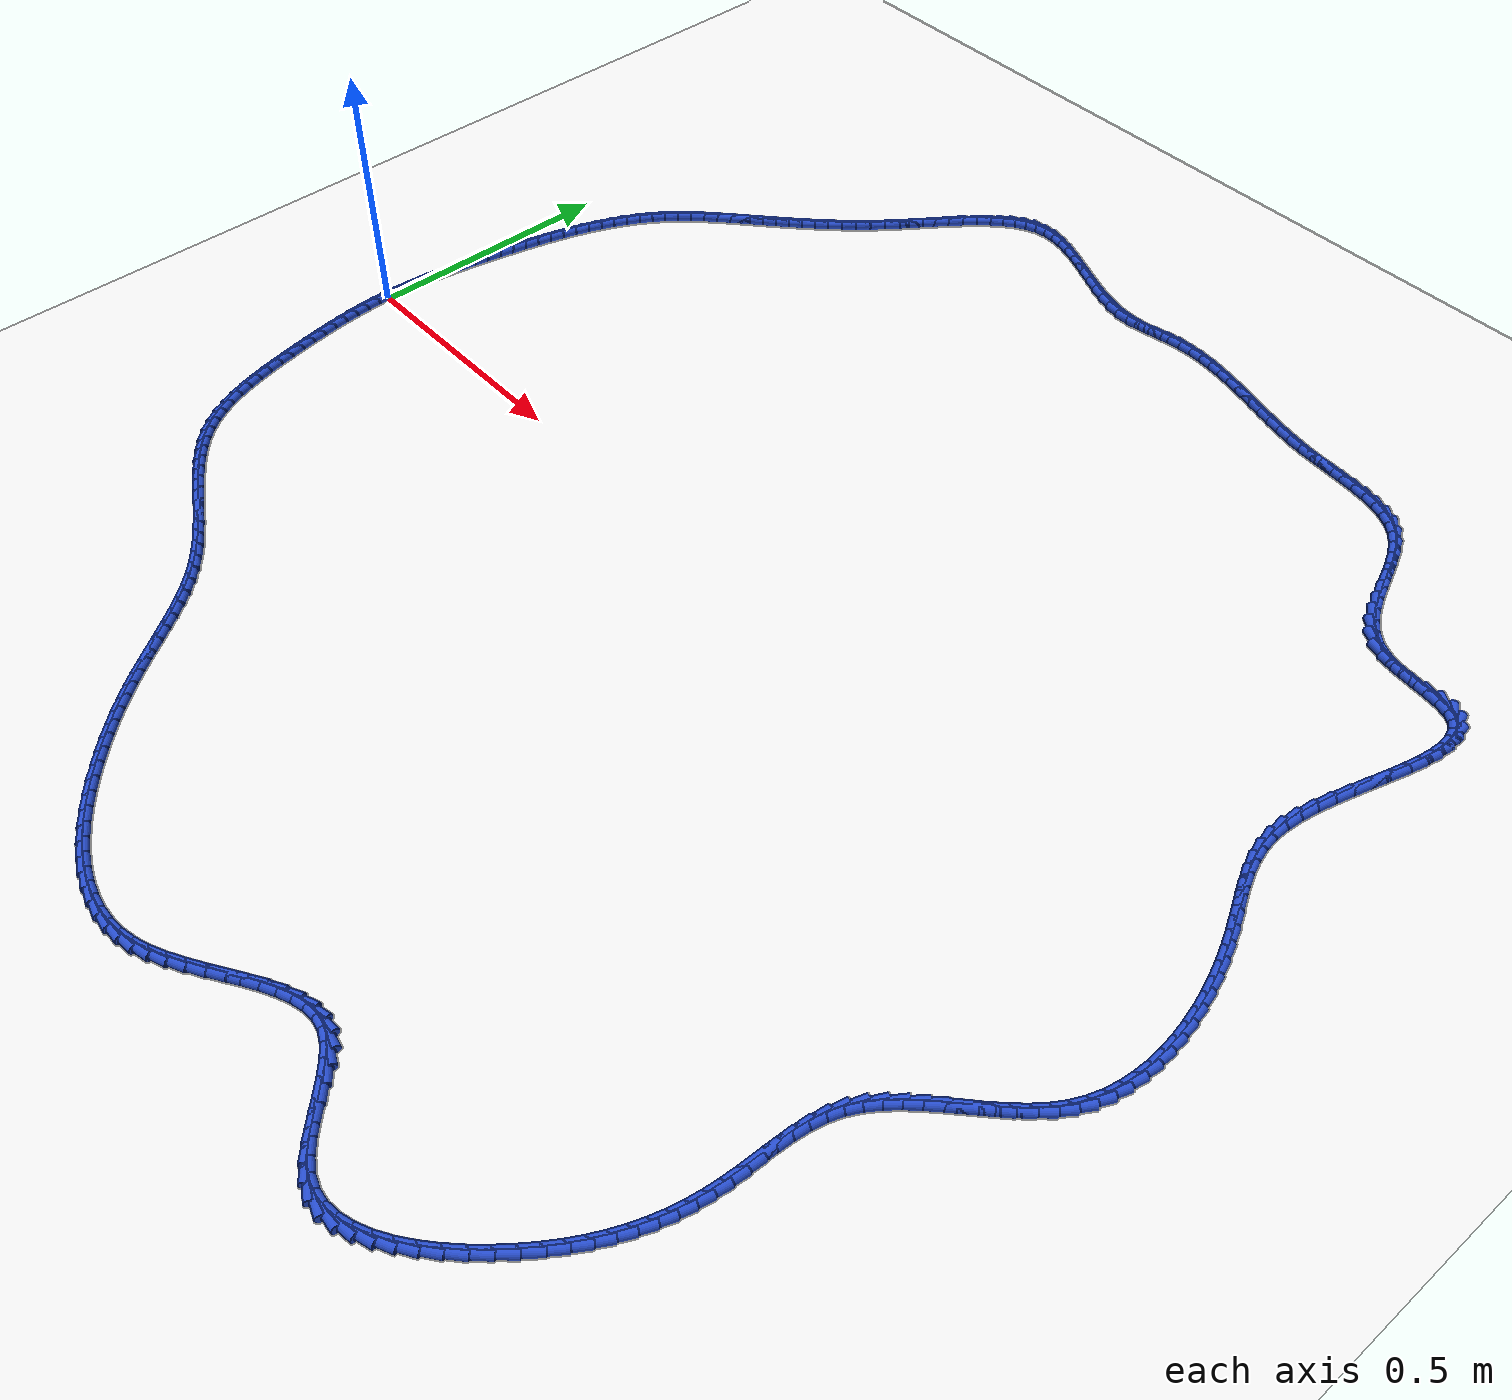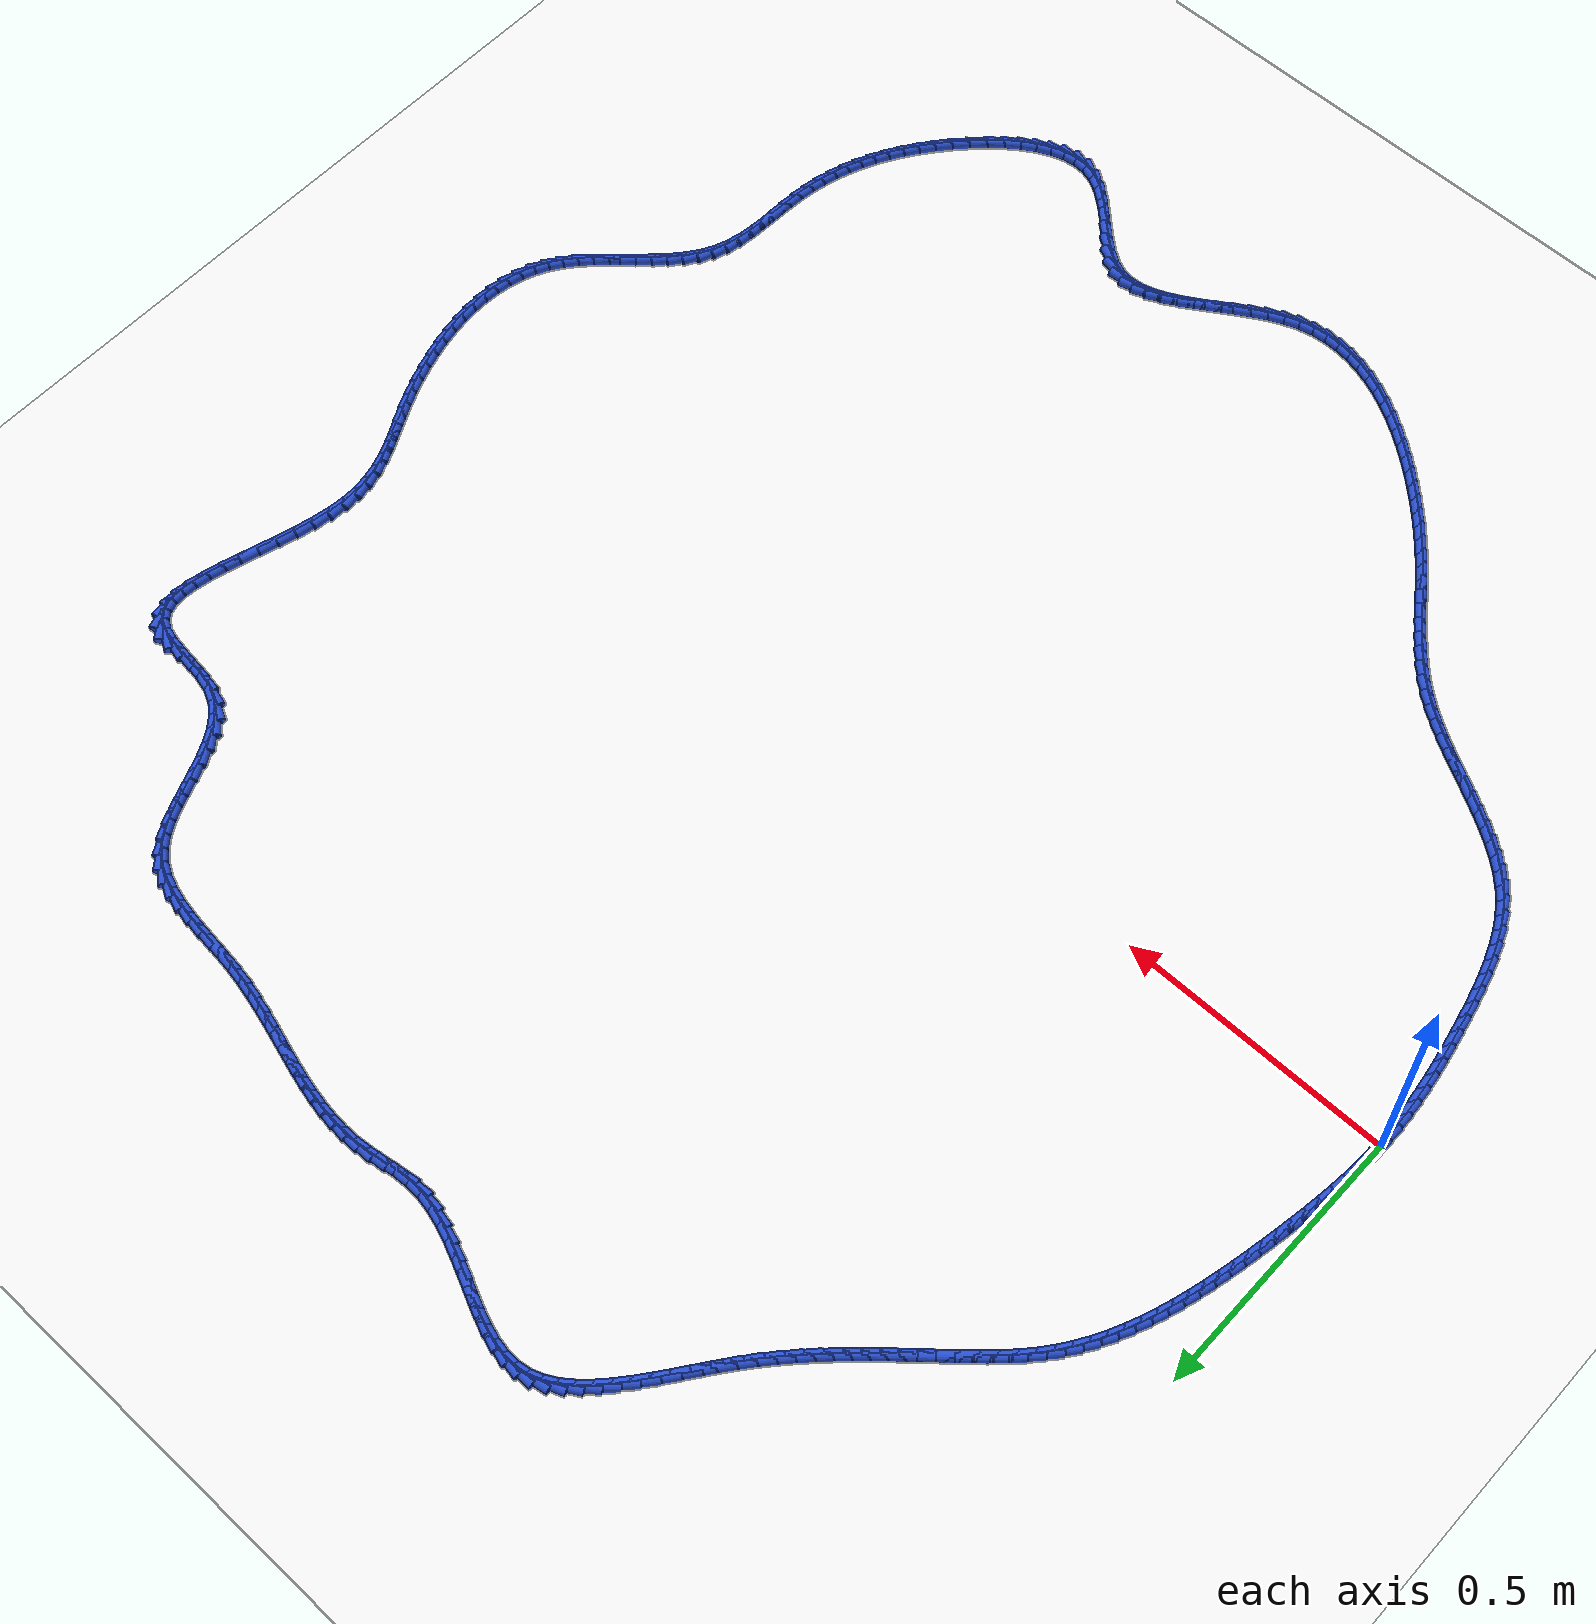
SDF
<sdf version="1.6">
 <world name="default">
  <light name="sun" type="directional">
   <pose>0 0 10 0 -0 0</pose>
   <diffuse>0.8 0.8 0.8 1</diffuse>
   <specular>0.2 0.2 0.2 1</specular>
   <attenuation>
    <range>1000</range>
    <constant>0.9</constant>
    <linear>0.01</linear>
    <quadratic>0.001</quadratic>
   </attenuation>
   <direction>-0.5 0.1 -0.9</direction>
  </light>
  <model name="ground_plane">
   <static>1</static>
   <link name="link">
    <collision name="collision">
     <geometry><plane><normal>0 0 1</normal><size>100 100</size></plane></geometry>
     <surface><friction><ode><mu>100</mu><mu2>50</mu2></ode></friction></surface>
    </collision>
    <visual name="visual">
     <cast_shadows>0</cast_shadows>
     <geometry><plane><normal>0 0 1</normal><size>100 100</size></plane></geometry>
     <material>
      <script><uri>file://media/materials/scripts/gazebo.material</uri><name>Gazebo/WhiteGlow</name></script>
     </material>
    </visual>
   </link>
  </model>
  <gravity>0 0 -9.8</gravity>
  <magnetic_field>6e-06 2.3e-05 -4.2e-05</magnetic_field>
  <atmosphere type="adiabatic"/>
  <physics name="default_physics" default="0" type="ode">
   <max_step_size>0.001</max_step_size>
   <real_time_factor>1</real_time_factor>
   <real_time_update_rate>1000</real_time_update_rate>
  </physics>
  <scene><ambient>0.4 0.4 0.4 1</ambient><background>0.7 0.7 0.7 1</background><shadows>1</shadows></scene>
  <spherical_coordinates>
   <surface_model>EARTH_WGS84</surface_model>
   <latitude_deg>0</latitude_deg>
   <longitude_deg>0</longitude_deg>
   <elevation>0</elevation>
   <heading_deg>0</heading_deg>
  </spherical_coordinates>
  <model name="line">
   <link name="link_0">
    <pose>6.938893903907228e-18 -2.0816681711721685e-17 0.01 0 1.57 1.5494531435086585</pose>
    <collision name="collision">
     <geometry><cylinder><radius>0.01</radius><length>0.08</length></cylinder></geometry>
    </collision>
    <visual name="visual">
     <material>
      <script><name>Gazebo/Blue</name><uri>file://media/materials/scripts/gazebo.material</uri></script>
     </material>
     <geometry><cylinder><radius>0.01</radius><length>0.08</length></cylinder></geometry>
    </visual>
   </link>
   <link name="link_1">
    <pose>0.0005825838232916123 0.027291868838746187 0.01 0 1.57 1.515931259168401</pose>
    <collision name="collision">
     <geometry><cylinder><radius>0.01</radius><length>0.08</length></cylinder></geometry>
    </collision>
    <visual name="visual">
     <material>
      <script><name>Gazebo/Blue</name><uri>file://media/materials/scripts/gazebo.material</uri></script>
     </material>
     <geometry><cylinder><radius>0.01</radius><length>0.08</length></cylinder></geometry>
    </visual>
   </link>
   <link name="link_2">
    <pose>0.0020831431300984845 0.054614415231058575 0.01 0 1.57 1.4859358087470094</pose>
    <collision name="collision">
     <geometry><cylinder><radius>0.01</radius><length>0.08</length></cylinder></geometry>
    </collision>
    <visual name="visual">
     <material>
      <script><name>Gazebo/Blue</name><uri>file://media/materials/scripts/gazebo.material</uri></script>
     </material>
     <geometry><cylinder><radius>0.01</radius><length>0.08</length></cylinder></geometry>
    </visual>
   </link>
   <link name="link_3">
    <pose>0.004410571160714683 0.08197506018530926 0.01 0 1.57 1.4594881915163689</pose>
    <collision name="collision">
     <geometry><cylinder><radius>0.01</radius><length>0.08</length></cylinder></geometry>
    </collision>
    <visual name="visual">
     <material>
      <script><name>Gazebo/Blue</name><uri>file://media/materials/scripts/gazebo.material</uri></script>
     </material>
     <geometry><cylinder><radius>0.01</radius><length>0.08</length></cylinder></geometry>
    </visual>
   </link>
   <link name="link_4">
    <pose>0.007473761155434266 0.10938122470987041 0.01 0 1.57 1.4365766252881271</pose>
    <collision name="collision">
     <geometry><cylinder><radius>0.01</radius><length>0.08</length></cylinder></geometry>
    </collision>
    <visual name="visual">
     <material>
      <script><name>Gazebo/Blue</name><uri>file://media/materials/scripts/gazebo.material</uri></script>
     </material>
     <geometry><cylinder><radius>0.01</radius><length>0.08</length></cylinder></geometry>
    </visual>
   </link>
   <link name="link_5">
    <pose>0.011181606354551284 0.13684032981311414 0.01 0 1.57 1.4171663608020437</pose>
    <collision name="collision">
     <geometry><cylinder><radius>0.01</radius><length>0.08</length></cylinder></geometry>
    </collision>
    <visual name="visual">
     <material>
      <script><name>Gazebo/Blue</name><uri>file://media/materials/scripts/gazebo.material</uri></script>
     </material>
     <geometry><cylinder><radius>0.01</radius><length>0.08</length></cylinder></geometry>
    </visual>
   </link>
   <link name="link_6">
    <pose>0.015442999998359797 0.16435979650341256 0.01 0 1.57 1.401208474222697</pose>
    <collision name="collision">
     <geometry><cylinder><radius>0.01</radius><length>0.08</length></cylinder></geometry>
    </collision>
    <visual name="visual">
     <material>
      <script><name>Gazebo/Blue</name><uri>file://media/materials/scripts/gazebo.material</uri></script>
     </material>
     <geometry><cylinder><radius>0.01</radius><length>0.08</length></cylinder></geometry>
    </visual>
   </link>
   <link name="link_7">
    <pose>0.02016683532715386 0.19194704578913788 0.01 0 1.57 1.388647062900531</pose>
    <collision name="collision">
     <geometry><cylinder><radius>0.01</radius><length>0.08</length></cylinder></geometry>
    </collision>
    <visual name="visual">
     <material>
      <script><name>Gazebo/Blue</name><uri>file://media/materials/scripts/gazebo.material</uri></script>
     </material>
     <geometry><cylinder><radius>0.01</radius><length>0.08</length></cylinder></geometry>
    </visual>
   </link>
   <link name="link_8">
    <pose>0.025262005581227535 0.2196094986786622 0.01 0 1.57 1.3793966796333932</pose>
    <collision name="collision">
     <geometry><cylinder><radius>0.01</radius><length>0.08</length></cylinder></geometry>
    </collision>
    <visual name="visual">
     <material>
      <script><name>Gazebo/Blue</name><uri>file://media/materials/scripts/gazebo.material</uri></script>
     </material>
     <geometry><cylinder><radius>0.01</radius><length>0.08</length></cylinder></geometry>
    </visual>
   </link>
   <link name="link_9">
    <pose>0.030638147203376143 0.24735422685794506 0.01 0 1.57 1.3710302161828525</pose>
    <collision name="collision">
     <geometry><cylinder><radius>0.01</radius><length>0.08</length></cylinder></geometry>
    </collision>
    <visual name="visual">
     <material>
      <script><name>Gazebo/Blue</name><uri>file://media/materials/scripts/gazebo.material</uri></script>
     </material>
     <geometry><cylinder><radius>0.01</radius><length>0.08</length></cylinder></geometry>
    </visual>
   </link>
   <link name="link_10">
    <pose>0.036267644909226696 0.2751588088694036 0.01 0 1.57 1.3593739814863635</pose>
    <collision name="collision">
     <geometry><cylinder><radius>0.01</radius><length>0.08</length></cylinder></geometry>
    </collision>
    <visual name="visual">
     <material>
      <script><name>Gazebo/Blue</name><uri>file://media/materials/scripts/gazebo.material</uri></script>
     </material>
     <geometry><cylinder><radius>0.01</radius><length>0.08</length></cylinder></geometry>
    </visual>
   </link>
   <link name="link_11">
    <pose>0.042232331299595624 0.30294938021100704 0.01 0 1.57 1.343964227864858</pose>
    <collision name="collision">
     <geometry><cylinder><radius>0.01</radius><length>0.08</length></cylinder></geometry>
    </collision>
    <visual name="visual">
     <material>
      <script><name>Gazebo/Blue</name><uri>file://media/materials/scripts/gazebo.material</uri></script>
     </material>
     <geometry><cylinder><radius>0.01</radius><length>0.08</length></cylinder></geometry>
    </visual>
   </link>
   <link name="link_12">
    <pose>0.0486250381578275 0.3306469065098339 0.01 0 1.57 1.3247170430544049</pose>
    <collision name="collision">
     <geometry><cylinder><radius>0.01</radius><length>0.08</length></cylinder></geometry>
    </collision>
    <visual name="visual">
     <material>
      <script><name>Gazebo/Blue</name><uri>file://media/materials/scripts/gazebo.material</uri></script>
     </material>
     <geometry><cylinder><radius>0.01</radius><length>0.08</length></cylinder></geometry>
    </visual>
   </link>
   <link name="link_13">
    <pose>0.05553859726726691 0.3581723533929629 0.01 0 1.57 1.301516769421281</pose>
    <collision name="collision">
     <geometry><cylinder><radius>0.01</radius><length>0.08</length></cylinder></geometry>
    </collision>
    <visual name="visual">
     <material>
      <script><name>Gazebo/Blue</name><uri>file://media/materials/scripts/gazebo.material</uri></script>
     </material>
     <geometry><cylinder><radius>0.01</radius><length>0.08</length></cylinder></geometry>
    </visual>
   </link>
   <link name="link_14">
    <pose>0.06306584041125841 0.3854466864874726 0.01 0 1.57 1.2742229018336808</pose>
    <collision name="collision">
     <geometry><cylinder><radius>0.01</radius><length>0.08</length></cylinder></geometry>
    </collision>
    <visual name="visual">
     <material>
      <script><name>Gazebo/Blue</name><uri>file://media/materials/scripts/gazebo.material</uri></script>
     </material>
     <geometry><cylinder><radius>0.01</radius><length>0.08</length></cylinder></geometry>
    </visual>
   </link>
   <link name="link_15">
    <pose>0.07129959937314657 0.41239087142044156 0.01 0 1.57 1.242679327505642</pose>
    <collision name="collision">
     <geometry><cylinder><radius>0.01</radius><length>0.08</length></cylinder></geometry>
    </collision>
    <visual name="visual">
     <material>
      <script><name>Gazebo/Blue</name><uri>file://media/materials/scripts/gazebo.material</uri></script>
     </material>
     <geometry><cylinder><radius>0.01</radius><length>0.08</length></cylinder></geometry>
    </visual>
   </link>
   <link name="link_16">
    <pose>0.08033270593627595 0.4389258738189481 0.01 0 1.57 1.2067268173624675</pose>
    <collision name="collision">
     <geometry><cylinder><radius>0.01</radius><length>0.08</length></cylinder></geometry>
    </collision>
    <visual name="visual">
     <material>
      <script><name>Gazebo/Blue</name><uri>file://media/materials/scripts/gazebo.material</uri></script>
     </material>
     <geometry><cylinder><radius>0.01</radius><length>0.08</length></cylinder></geometry>
    </visual>
   </link>
   <link name="link_17">
    <pose>0.09025799188399117 0.46497265931007126 0.01 0 1.57 1.1662196836590046</pose>
    <collision name="collision">
     <geometry><cylinder><radius>0.01</radius><length>0.08</length></cylinder></geometry>
    </collision>
    <visual name="visual">
     <material>
      <script><name>Gazebo/Blue</name><uri>file://media/materials/scripts/gazebo.material</uri></script>
     </material>
     <geometry><cylinder><radius>0.01</radius><length>0.08</length></cylinder></geometry>
    </visual>
   </link>
   <link name="link_18">
    <pose>0.10116828899963673 0.49045219352088926 0.01 0 1.57 1.1210473194514161</pose>
    <collision name="collision">
     <geometry><cylinder><radius>0.01</radius><length>0.08</length></cylinder></geometry>
    </collision>
    <visual name="visual">
     <material>
      <script><name>Gazebo/Blue</name><uri>file://media/materials/scripts/gazebo.material</uri></script>
     </material>
     <geometry><cylinder><radius>0.01</radius><length>0.08</length></cylinder></geometry>
    </visual>
   </link>
   <link name="link_19">
    <pose>0.11315642906655723 0.5152854420784809 0.01 0 1.57 1.0711607935965868</pose>
    <collision name="collision">
     <geometry><cylinder><radius>0.01</radius><length>0.08</length></cylinder></geometry>
    </collision>
    <visual name="visual">
     <material>
      <script><name>Gazebo/Blue</name><uri>file://media/materials/scripts/gazebo.material</uri></script>
     </material>
     <geometry><cylinder><radius>0.01</radius><length>0.08</length></cylinder></geometry>
    </visual>
   </link>
   <link name="link_20">
    <pose>0.12631524386809725 0.5393933706099246 0.01 0 1.57 1.016603648147927</pose>
    <collision name="collision">
     <geometry><cylinder><radius>0.01</radius><length>0.08</length></cylinder></geometry>
    </collision>
    <visual name="visual">
     <material>
      <script><name>Gazebo/Blue</name><uri>file://media/materials/scripts/gazebo.material</uri></script>
     </material>
     <geometry><cylinder><radius>0.01</radius><length>0.08</length></cylinder></geometry>
    </visual>
   </link>
   <link name="link_21">
    <pose>0.1407375651876014 0.5626969447422993 0.01 0 1.57 0.9575444677504552</pose>
    <collision name="collision">
     <geometry><cylinder><radius>0.01</radius><length>0.08</length></cylinder></geometry>
    </collision>
    <visual name="visual">
     <material>
      <script><name>Gazebo/Blue</name><uri>file://media/materials/scripts/gazebo.material</uri></script>
     </material>
     <geometry><cylinder><radius>0.01</radius><length>0.08</length></cylinder></geometry>
    </visual>
   </link>
   <link name="link_22">
    <pose>0.15651622480841415 0.585117130102683 0.01 0 1.57 0.8946184165654034</pose>
    <collision name="collision">
     <geometry><cylinder><radius>0.01</radius><length>0.08</length></cylinder></geometry>
    </collision>
    <visual name="visual">
     <material>
      <script><name>Gazebo/Blue</name><uri>file://media/materials/scripts/gazebo.material</uri></script>
     </material>
     <geometry><cylinder><radius>0.01</radius><length>0.08</length></cylinder></geometry>
    </visual>
   </link>
   <link name="link_23">
    <pose>0.17373627909197395 0.6065789033945376 0.01 0 1.57 0.836023580005325</pose>
    <collision name="collision">
     <geometry><cylinder><radius>0.01</radius><length>0.08</length></cylinder></geometry>
    </collision>
    <visual name="visual">
     <material>
      <script><name>Gazebo/Blue</name><uri>file://media/materials/scripts/gazebo.material</uri></script>
     </material>
     <geometry><cylinder><radius>0.01</radius><length>0.08</length></cylinder></geometry>
    </visual>
   </link>
   <link name="link_24">
    <pose>0.19228601286615007 0.627108749080089 0.01 0 1.57 0.7897481582650647</pose>
    <collision name="collision">
     <geometry><cylinder><radius>0.01</radius><length>0.08</length></cylinder></geometry>
    </collision>
    <visual name="visual">
     <material>
      <script><name>Gazebo/Blue</name><uri>file://media/materials/scripts/gazebo.material</uri></script>
     </material>
     <geometry><cylinder><radius>0.01</radius><length>0.08</length></cylinder></geometry>
    </visual>
   </link>
   <link name="link_25">
    <pose>0.21184642646782254 0.6468400826584106 0.01 0 1.57 0.7556238388812125</pose>
    <collision name="collision">
     <geometry><cylinder><radius>0.01</radius><length>0.08</length></cylinder></geometry>
    </collision>
    <visual name="visual">
     <material>
      <script><name>Gazebo/Blue</name><uri>file://media/materials/scripts/gazebo.material</uri></script>
     </material>
     <geometry><cylinder><radius>0.01</radius><length>0.08</length></cylinder></geometry>
    </visual>
   </link>
   <link name="link_26">
    <pose>0.23208864043470145 0.6659114162818012 0.01 0 1.57 0.7331965562980377</pose>
    <collision name="collision">
     <geometry><cylinder><radius>0.01</radius><length>0.08</length></cylinder></geometry>
    </collision>
    <visual name="visual">
     <material>
      <script><name>Gazebo/Blue</name><uri>file://media/materials/scripts/gazebo.material</uri></script>
     </material>
     <geometry><cylinder><radius>0.01</radius><length>0.08</length></cylinder></geometry>
    </visual>
   </link>
   <link name="link_27">
    <pose>0.25268377530449676 0.6844612621025574 0.01 0 1.57 0.7220689563805252</pose>
    <collision name="collision">
     <geometry><cylinder><radius>0.01</radius><length>0.08</length></cylinder></geometry>
    </collision>
    <visual name="visual">
     <material>
      <script><name>Gazebo/Blue</name><uri>file://media/materials/scripts/gazebo.material</uri></script>
     </material>
     <geometry><cylinder><radius>0.01</radius><length>0.08</length></cylinder></geometry>
    </visual>
   </link>
   <link name="link_28">
    <pose>0.27331071656711353 0.7026281323857229 0.01 0 1.57 0.7184831092377628</pose>
    <collision name="collision">
     <geometry><cylinder><radius>0.01</radius><length>0.08</length></cylinder></geometry>
    </collision>
    <visual name="visual">
     <material>
      <script><name>Gazebo/Blue</name><uri>file://media/materials/scripts/gazebo.material</uri></script>
     </material>
     <geometry><cylinder><radius>0.01</radius><length>0.08</length></cylinder></geometry>
    </visual>
   </link>
   <link name="link_29">
    <pose>0.2938078131896725 0.7205505417117236 0.01 0 1.57 0.7189898173264087</pose>
    <collision name="collision">
     <geometry><cylinder><radius>0.01</radius><length>0.08</length></cylinder></geometry>
    </collision>
    <visual name="visual">
     <material>
      <script><name>Gazebo/Blue</name><uri>file://media/materials/scripts/gazebo.material</uri></script>
     </material>
     <geometry><cylinder><radius>0.01</radius><length>0.08</length></cylinder></geometry>
    </visual>
   </link>
   <link name="link_30">
    <pose>0.3141629223896402 0.7383670068318198 0.01 0 1.57 0.7235231356761888</pose>
    <collision name="collision">
     <geometry><cylinder><radius>0.01</radius><length>0.08</length></cylinder></geometry>
    </collision>
    <visual name="visual">
     <material>
      <script><name>Gazebo/Blue</name><uri>file://media/materials/scripts/gazebo.material</uri></script>
     </material>
     <geometry><cylinder><radius>0.01</radius><length>0.08</length></cylinder></geometry>
    </visual>
   </link>
   <link name="link_31">
    <pose>0.3343696726972589 0.7562160445810704 0.01 0 1.57 0.732079214448538</pose>
    <collision name="collision">
     <geometry><cylinder><radius>0.01</radius><length>0.08</length></cylinder></geometry>
    </collision>
    <visual name="visual">
     <material>
      <script><name>Gazebo/Blue</name><uri>file://media/materials/scripts/gazebo.material</uri></script>
     </material>
     <geometry><cylinder><radius>0.01</radius><length>0.08</length></cylinder></geometry>
    </visual>
   </link>
   <link name="link_32">
    <pose>0.35442169264277107 0.7742361717945343 0.01 0 1.57 0.7445742330993187</pose>
    <collision name="collision">
     <geometry><cylinder><radius>0.01</radius><length>0.08</length></cylinder></geometry>
    </collision>
    <visual name="visual">
     <material>
      <script><name>Gazebo/Blue</name><uri>file://media/materials/scripts/gazebo.material</uri></script>
     </material>
     <geometry><cylinder><radius>0.01</radius><length>0.08</length></cylinder></geometry>
    </visual>
   </link>
   <link name="link_33">
    <pose>0.37431261075641875 0.7925659053072703 0.01 0 1.57 0.7608431983652604</pose>
    <collision name="collision">
     <geometry><cylinder><radius>0.01</radius><length>0.08</length></cylinder></geometry>
    </collision>
    <visual name="visual">
     <material>
      <script><name>Gazebo/Blue</name><uri>file://media/materials/scripts/gazebo.material</uri></script>
     </material>
     <geometry><cylinder><radius>0.01</radius><length>0.08</length></cylinder></geometry>
    </visual>
   </link>
   <link name="link_34">
    <pose>0.39403605556844457 0.8113437619543372 0.01 0 1.57 0.7806414802405397</pose>
    <collision name="collision">
     <geometry><cylinder><radius>0.01</radius><length>0.08</length></cylinder></geometry>
    </collision>
    <visual name="visual">
     <material>
      <script><name>Gazebo/Blue</name><uri>file://media/materials/scripts/gazebo.material</uri></script>
     </material>
     <geometry><cylinder><radius>0.01</radius><length>0.08</length></cylinder></geometry>
    </visual>
   </link>
   <link name="link_35">
    <pose>0.41358565560909066 0.8307082585707939 0.01 0 1.57 0.8036497400095954</pose>
    <collision name="collision">
     <geometry><cylinder><radius>0.01</radius><length>0.08</length></cylinder></geometry>
    </collision>
    <visual name="visual">
     <material>
      <script><name>Gazebo/Blue</name><uri>file://media/materials/scripts/gazebo.material</uri></script>
     </material>
     <geometry><cylinder><radius>0.01</radius><length>0.08</length></cylinder></geometry>
    </visual>
   </link>
   <link name="link_36">
    <pose>0.4329550394085992 0.8507979119916991 0.01 0 1.57 0.829482736224326</pose>
    <collision name="collision">
     <geometry><cylinder><radius>0.01</radius><length>0.08</length></cylinder></geometry>
    </collision>
    <visual name="visual">
     <material>
      <script><name>Gazebo/Blue</name><uri>file://media/materials/scripts/gazebo.material</uri></script>
     </material>
     <geometry><cylinder><radius>0.01</radius><length>0.08</length></cylinder></geometry>
    </visual>
   </link>
   <link name="link_37">
    <pose>0.45213783549721265 0.8717512390521117 0.01 0 1.57 0.8577021111829118</pose>
    <collision name="collision">
     <geometry><cylinder><radius>0.01</radius><length>0.08</length></cylinder></geometry>
    </collision>
    <visual name="visual">
     <material>
      <script><name>Gazebo/Blue</name><uri>file://media/materials/scripts/gazebo.material</uri></script>
     </material>
     <geometry><cylinder><radius>0.01</radius><length>0.08</length></cylinder></geometry>
    </visual>
   </link>
   <link name="link_38">
    <pose>0.4711276724051735 0.8937067565870908 0.01 0 1.57 0.8878327082598387</pose>
    <collision name="collision">
     <geometry><cylinder><radius>0.01</radius><length>0.08</length></cylinder></geometry>
    </collision>
    <visual name="visual">
     <material>
      <script><name>Gazebo/Blue</name><uri>file://media/materials/scripts/gazebo.material</uri></script>
     </material>
     <geometry><cylinder><radius>0.01</radius><length>0.08</length></cylinder></geometry>
    </visual>
   </link>
   <link name="link_39">
    <pose>0.4899181786736791 0.9168029813638459 0.01 0 1.57 0.9166592646081043</pose>
    <collision name="collision">
     <geometry><cylinder><radius>0.01</radius><length>0.08</length></cylinder></geometry>
    </collision>
    <visual name="visual">
     <material>
      <script><name>Gazebo/Blue</name><uri>file://media/materials/scripts/gazebo.material</uri></script>
     </material>
     <geometry><cylinder><radius>0.01</radius><length>0.08</length></cylinder></geometry>
    </visual>
   </link>
   <link name="link_40">
    <pose>0.5085212726804981 0.9410651561491807 0.01 0 1.57 0.9339773057644073</pose>
    <collision name="collision">
     <geometry><cylinder><radius>0.01</radius><length>0.08</length></cylinder></geometry>
    </collision>
    <visual name="visual">
     <material>
      <script><name>Gazebo/Blue</name><uri>file://media/materials/scripts/gazebo.material</uri></script>
     </material>
     <geometry><cylinder><radius>0.01</radius><length>0.08</length></cylinder></geometry>
    </visual>
   </link>
   <link name="link_41">
    <pose>0.5270201900717003 0.9660768362050959 0.01 0 1.57 0.9383528872575571</pose>
    <collision name="collision">
     <geometry><cylinder><radius>0.01</radius><length>0.08</length></cylinder></geometry>
    </collision>
    <visual name="visual">
     <material>
      <script><name>Gazebo/Blue</name><uri>file://media/materials/scripts/gazebo.material</uri></script>
     </material>
     <geometry><cylinder><radius>0.01</radius><length>0.08</length></cylinder></geometry>
    </visual>
   </link>
   <link name="link_42">
    <pose>0.5455155468287546 0.991313935584696 0.01 0 1.57 0.9301605549803177</pose>
    <collision name="collision">
     <geometry><cylinder><radius>0.01</radius><length>0.08</length></cylinder></geometry>
    </collision>
    <visual name="visual">
     <material>
      <script><name>Gazebo/Blue</name><uri>file://media/materials/scripts/gazebo.material</uri></script>
     </material>
     <geometry><cylinder><radius>0.01</radius><length>0.08</length></cylinder></geometry>
    </visual>
   </link>
   <link name="link_43">
    <pose>0.5641079589331288 1.0162523683410845 0.01 0 1.57 0.9088896641070441</pose>
    <collision name="collision">
     <geometry><cylinder><radius>0.01</radius><length>0.08</length></cylinder></geometry>
    </collision>
    <visual name="visual">
     <material>
      <script><name>Gazebo/Blue</name><uri>file://media/materials/scripts/gazebo.material</uri></script>
     </material>
     <geometry><cylinder><radius>0.01</radius><length>0.08</length></cylinder></geometry>
    </visual>
   </link>
   <link name="link_44">
    <pose>0.5828980423662917 1.0403680485273656 0.01 0 1.57 0.8731017928134122</pose>
    <collision name="collision">
     <geometry><cylinder><radius>0.01</radius><length>0.08</length></cylinder></geometry>
    </collision>
    <visual name="visual">
     <material>
      <script><name>Gazebo/Blue</name><uri>file://media/materials/scripts/gazebo.material</uri></script>
     </material>
     <geometry><cylinder><radius>0.01</radius><length>0.08</length></cylinder></geometry>
    </visual>
   </link>
   <link name="link_45">
    <pose>0.6019864131097119 1.0631368901966443 0.01 0 1.57 0.8203136818103788</pose>
    <collision name="collision">
     <geometry><cylinder><radius>0.01</radius><length>0.08</length></cylinder></geometry>
    </collision>
    <visual name="visual">
     <material>
      <script><name>Gazebo/Blue</name><uri>file://media/materials/scripts/gazebo.material</uri></script>
     </material>
     <geometry><cylinder><radius>0.01</radius><length>0.08</length></cylinder></geometry>
    </visual>
   </link>
   <link name="link_46">
    <pose>0.621473687144858 1.0840348074020243 0.01 0 1.57 0.7468644261123002</pose>
    <collision name="collision">
     <geometry><cylinder><radius>0.01</radius><length>0.08</length></cylinder></geometry>
    </collision>
    <visual name="visual">
     <material>
      <script><name>Gazebo/Blue</name><uri>file://media/materials/scripts/gazebo.material</uri></script>
     </material>
     <geometry><cylinder><radius>0.01</radius><length>0.08</length></cylinder></geometry>
    </visual>
   </link>
   <link name="link_47">
    <pose>0.6414604804531984 1.1025377141966106 0.01 0 1.57 0.6479508072377705</pose>
    <collision name="collision">
     <geometry><cylinder><radius>0.01</radius><length>0.08</length></cylinder></geometry>
    </collision>
    <visual name="visual">
     <material>
      <script><name>Gazebo/Blue</name><uri>file://media/materials/scripts/gazebo.material</uri></script>
     </material>
     <geometry><cylinder><radius>0.01</radius><length>0.08</length></cylinder></geometry>
    </visual>
   </link>
   <link name="link_48">
    <pose>0.6620474090162014 1.1181215246335066 0.01 0 1.57 0.5183043014613671</pose>
    <collision name="collision">
     <geometry><cylinder><radius>0.01</radius><length>0.08</length></cylinder></geometry>
    </collision>
    <visual name="visual">
     <material>
      <script><name>Gazebo/Blue</name><uri>file://media/materials/scripts/gazebo.material</uri></script>
     </material>
     <geometry><cylinder><radius>0.01</radius><length>0.08</length></cylinder></geometry>
    </visual>
   </link>
   <link name="link_49">
    <pose>0.6833350888153358 1.1302621527658172 0.01 0 1.57 0.3543963441429075</pose>
    <collision name="collision">
     <geometry><cylinder><radius>0.01</radius><length>0.08</length></cylinder></geometry>
    </collision>
    <visual name="visual">
     <material>
      <script><name>Gazebo/Blue</name><uri>file://media/materials/scripts/gazebo.material</uri></script>
     </material>
     <geometry><cylinder><radius>0.01</radius><length>0.08</length></cylinder></geometry>
    </visual>
   </link>
   <link name="link_50">
    <pose>0.7054241358320703 1.1384355126466466 0.01 0 1.57 0.15952265452041242</pose>
    <collision name="collision">
     <geometry><cylinder><radius>0.01</radius><length>0.08</length></cylinder></geometry>
    </collision>
    <visual name="visual">
     <material>
      <script><name>Gazebo/Blue</name><uri>file://media/materials/scripts/gazebo.material</uri></script>
     </material>
     <geometry><cylinder><radius>0.01</radius><length>0.08</length></cylinder></geometry>
    </visual>
   </link>
   <link name="link_51">
    <pose>0.7284126194850585 1.1421341233742 0.01 0 1.57 -0.030824034987810355</pose>
    <collision name="collision">
     <geometry><cylinder><radius>0.01</radius><length>0.08</length></cylinder></geometry>
    </collision>
    <visual name="visual">
     <material>
      <script><name>Gazebo/Blue</name><uri>file://media/materials/scripts/gazebo.material</uri></script>
     </material>
     <geometry><cylinder><radius>0.01</radius><length>0.08</length></cylinder></geometry>
    </visual>
   </link>
   <link name="link_52">
    <pose>0.7523147783640864 1.1413971289665221 0.01 0 1.57 -0.17905438845074315</pose>
    <collision name="collision">
     <geometry><cylinder><radius>0.01</radius><length>0.08</length></cylinder></geometry>
    </collision>
    <visual name="visual">
     <material>
      <script><name>Gazebo/Blue</name><uri>file://media/materials/scripts/gazebo.material</uri></script>
     </material>
     <geometry><cylinder><radius>0.01</radius><length>0.08</length></cylinder></geometry>
    </visual>
   </link>
   <link name="link_53">
    <pose>0.7770439939159024 1.136921319661698 0.01 0 1.57 -0.28567090460512023</pose>
    <collision name="collision">
     <geometry><cylinder><radius>0.01</radius><length>0.08</length></cylinder></geometry>
    </collision>
    <visual name="visual">
     <material>
      <script><name>Gazebo/Blue</name><uri>file://media/materials/scripts/gazebo.material</uri></script>
     </material>
     <geometry><cylinder><radius>0.01</radius><length>0.08</length></cylinder></geometry>
    </visual>
   </link>
   <link name="link_54">
    <pose>0.8025076592235597 1.1294425332519054 0.01 0 1.57 -0.35730429045220624</pose>
    <collision name="collision">
     <geometry><cylinder><radius>0.01</radius><length>0.08</length></cylinder></geometry>
    </collision>
    <visual name="visual">
     <material>
      <script><name>Gazebo/Blue</name><uri>file://media/materials/scripts/gazebo.material</uri></script>
     </material>
     <geometry><cylinder><radius>0.01</radius><length>0.08</length></cylinder></geometry>
    </visual>
   </link>
   <link name="link_55">
    <pose>0.8286131673701104 1.1196966075293189 0.01 0 1.57 -0.40024766200278244</pose>
    <collision name="collision">
     <geometry><cylinder><radius>0.01</radius><length>0.08</length></cylinder></geometry>
    </collision>
    <visual name="visual">
     <material>
      <script><name>Gazebo/Blue</name><uri>file://media/materials/scripts/gazebo.material</uri></script>
     </material>
     <geometry><cylinder><radius>0.01</radius><length>0.08</length></cylinder></geometry>
    </visual>
   </link>
   <link name="link_56">
    <pose>0.8552679114386079 1.1084193802861162 0.01 0 1.57 -0.4189384292275789</pose>
    <collision name="collision">
     <geometry><cylinder><radius>0.01</radius><length>0.08</length></cylinder></geometry>
    </collision>
    <visual name="visual">
     <material>
      <script><name>Gazebo/Blue</name><uri>file://media/materials/scripts/gazebo.material</uri></script>
     </material>
     <geometry><cylinder><radius>0.01</radius><length>0.08</length></cylinder></geometry>
    </visual>
   </link>
   <link name="link_57">
    <pose>0.8823792845121055 1.0963466893144738 0.01 0 1.57 -0.41582166457328296</pose>
    <collision name="collision">
     <geometry><cylinder><radius>0.01</radius><length>0.08</length></cylinder></geometry>
    </collision>
    <visual name="visual">
     <material>
      <script><name>Gazebo/Blue</name><uri>file://media/materials/scripts/gazebo.material</uri></script>
     </material>
     <geometry><cylinder><radius>0.01</radius><length>0.08</length></cylinder></geometry>
    </visual>
   </link>
   <link name="link_58">
    <pose>0.9098546796736561 1.0842143724065676 0.01 0 1.57 -0.3915603402157383</pose>
    <collision name="collision">
     <geometry><cylinder><radius>0.01</radius><length>0.08</length></cylinder></geometry>
    </collision>
    <visual name="visual">
     <material>
      <script><name>Gazebo/Blue</name><uri>file://media/materials/scripts/gazebo.material</uri></script>
     </material>
     <geometry><cylinder><radius>0.01</radius><length>0.08</length></cylinder></geometry>
    </visual>
   </link>
   <link name="link_59">
    <pose>0.9376014900063123 1.072758267354575 0.01 0 1.57 -0.3452649383062241</pose>
    <collision name="collision">
     <geometry><cylinder><radius>0.01</radius><length>0.08</length></cylinder></geometry>
    </collision>
    <visual name="visual">
     <material>
      <script><name>Gazebo/Blue</name><uri>file://media/materials/scripts/gazebo.material</uri></script>
     </material>
     <geometry><cylinder><radius>0.01</radius><length>0.08</length></cylinder></geometry>
    </visual>
   </link>
   <link name="link_60">
    <pose>0.9655271085931276 1.0627142119506725 0.01 0 1.57 -0.2747576616143301</pose>
    <collision name="collision">
     <geometry><cylinder><radius>0.01</radius><length>0.08</length></cylinder></geometry>
    </collision>
    <visual name="visual">
     <material>
      <script><name>Gazebo/Blue</name><uri>file://media/materials/scripts/gazebo.material</uri></script>
     </material>
     <geometry><cylinder><radius>0.01</radius><length>0.08</length></cylinder></geometry>
    </visual>
   </link>
   <link name="link_61">
    <pose>0.9935389285171548 1.0548180439870365 0.01 0 1.57 -0.17710593868156585</pose>
    <collision name="collision">
     <geometry><cylinder><radius>0.01</radius><length>0.08</length></cylinder></geometry>
    </collision>
    <visual name="visual">
     <material>
      <script><name>Gazebo/Blue</name><uri>file://media/materials/scripts/gazebo.material</uri></script>
     </material>
     <geometry><cylinder><radius>0.01</radius><length>0.08</length></cylinder></geometry>
    </visual>
   </link>
   <link name="link_62">
    <pose>1.0215443428614468 1.0498056012558432 0.01 0 1.57 -0.05012006672405184</pose>
    <collision name="collision">
     <geometry><cylinder><radius>0.01</radius><length>0.08</length></cylinder></geometry>
    </collision>
    <visual name="visual">
     <material>
      <script><name>Gazebo/Blue</name><uri>file://media/materials/scripts/gazebo.material</uri></script>
     </material>
     <geometry><cylinder><radius>0.01</radius><length>0.08</length></cylinder></geometry>
    </visual>
   </link>
   <link name="link_63">
    <pose>1.0494509088871486 1.0484057499562558 0.01 0 1.57 0.07689102487371006</pose>
    <collision name="collision">
     <geometry><cylinder><radius>0.01</radius><length>0.08</length></cylinder></geometry>
    </collision>
    <visual name="visual">
     <material>
      <script><name>Gazebo/Blue</name><uri>file://media/materials/scripts/gazebo.material</uri></script>
     </material>
     <geometry><cylinder><radius>0.01</radius><length>0.08</length></cylinder></geometry>
    </visual>
   </link>
   <link name="link_64">
    <pose>1.0771851384512288 1.0505424758903719 0.01 0 1.57 0.14625126549340506</pose>
    <collision name="collision">
     <geometry><cylinder><radius>0.01</radius><length>0.08</length></cylinder></geometry>
    </collision>
    <visual name="visual">
     <material>
      <script><name>Gazebo/Blue</name><uri>file://media/materials/scripts/gazebo.material</uri></script>
     </material>
     <geometry><cylinder><radius>0.01</radius><length>0.08</length></cylinder></geometry>
    </visual>
   </link>
   <link name="link_65">
    <pose>1.104709875993688 1.054596952545493 0.01 0 1.57 0.1519937386249445</pose>
    <collision name="collision">
     <geometry><cylinder><radius>0.01</radius><length>0.08</length></cylinder></geometry>
    </collision>
    <visual name="visual">
     <material>
      <script><name>Gazebo/Blue</name><uri>file://media/materials/scripts/gazebo.material</uri></script>
     </material>
     <geometry><cylinder><radius>0.01</radius><length>0.08</length></cylinder></geometry>
    </visual>
   </link>
   <link name="link_66">
    <pose>1.131992074109087 1.0587759063722615 0.01 0 1.57 0.09530232501402217</pose>
    <collision name="collision">
     <geometry><cylinder><radius>0.01</radius><length>0.08</length></cylinder></geometry>
    </collision>
    <visual name="visual">
     <material>
      <script><name>Gazebo/Blue</name><uri>file://media/materials/scripts/gazebo.material</uri></script>
     </material>
     <geometry><cylinder><radius>0.01</radius><length>0.08</length></cylinder></geometry>
    </visual>
   </link>
   <link name="link_67">
    <pose>1.1590022559856203 1.0613578611379793 0.01 0 1.57 0.01378947042779266</pose>
    <collision name="collision">
     <geometry><cylinder><radius>0.01</radius><length>0.08</length></cylinder></geometry>
    </collision>
    <visual name="visual">
     <material>
      <script><name>Gazebo/Blue</name><uri>file://media/materials/scripts/gazebo.material</uri></script>
     </material>
     <geometry><cylinder><radius>0.01</radius><length>0.08</length></cylinder></geometry>
    </visual>
   </link>
   <link name="link_68">
    <pose>1.185765928079853 1.0617269413966333 0.01 0 1.57 -0.059820578594192306</pose>
    <collision name="collision">
     <geometry><cylinder><radius>0.01</radius><length>0.08</length></cylinder></geometry>
    </collision>
    <visual name="visual">
     <material>
      <script><name>Gazebo/Blue</name><uri>file://media/materials/scripts/gazebo.material</uri></script>
     </material>
     <geometry><cylinder><radius>0.01</radius><length>0.08</length></cylinder></geometry>
    </visual>
   </link>
   <link name="link_69">
    <pose>1.2123517336011567 1.0601346633514965 0.01 0 1.57 -0.12320681849378456</pose>
    <collision name="collision">
     <geometry><cylinder><radius>0.01</radius><length>0.08</length></cylinder></geometry>
    </collision>
    <visual name="visual">
     <material>
      <script><name>Gazebo/Blue</name><uri>file://media/materials/scripts/gazebo.material</uri></script>
     </material>
     <geometry><cylinder><radius>0.01</radius><length>0.08</length></cylinder></geometry>
    </visual>
   </link>
   <link name="link_70">
    <pose>1.2388294732313987 1.0568558176043839 0.01 0 1.57 -0.17558293454779447</pose>
    <collision name="collision">
     <geometry><cylinder><radius>0.01</radius><length>0.08</length></cylinder></geometry>
    </collision>
    <visual name="visual">
     <material>
      <script><name>Gazebo/Blue</name><uri>file://media/materials/scripts/gazebo.material</uri></script>
     </material>
     <geometry><cylinder><radius>0.01</radius><length>0.08</length></cylinder></geometry>
    </visual>
   </link>
   <link name="link_71">
    <pose>1.265268947652444 1.0521651947571082 0.01 0 1.57 -0.2166939707750178</pose>
    <collision name="collision">
     <geometry><cylinder><radius>0.01</radius><length>0.08</length></cylinder></geometry>
    </collision>
    <visual name="visual">
     <material>
      <script><name>Gazebo/Blue</name><uri>file://media/materials/scripts/gazebo.material</uri></script>
     </material>
     <geometry><cylinder><radius>0.01</radius><length>0.08</length></cylinder></geometry>
    </visual>
   </link>
   <link name="link_72">
    <pose>1.29173995754616 1.046337585411485 0.01 0 1.57 -0.24663272659543328</pose>
    <collision name="collision">
     <geometry><cylinder><radius>0.01</radius><length>0.08</length></cylinder></geometry>
    </collision>
    <visual name="visual">
     <material>
      <script><name>Gazebo/Blue</name><uri>file://media/materials/scripts/gazebo.material</uri></script>
     </material>
     <geometry><cylinder><radius>0.01</radius><length>0.08</length></cylinder></geometry>
    </visual>
   </link>
   <link name="link_73">
    <pose>1.3183123035944124 1.0396477801693271 0.01 0 1.57 -0.2656788623500307</pose>
    <collision name="collision">
     <geometry><cylinder><radius>0.01</radius><length>0.08</length></cylinder></geometry>
    </collision>
    <visual name="visual">
     <material>
      <script><name>Gazebo/Blue</name><uri>file://media/materials/scripts/gazebo.material</uri></script>
     </material>
     <geometry><cylinder><radius>0.01</radius><length>0.08</length></cylinder></geometry>
    </visual>
   </link>
   <link name="link_74">
    <pose>1.3450557864790686 1.0323705696324492 0.01 0 1.57 -0.27418314501500374</pose>
    <collision name="collision">
     <geometry><cylinder><radius>0.01</radius><length>0.08</length></cylinder></geometry>
    </collision>
    <visual name="visual">
     <material>
      <script><name>Gazebo/Blue</name><uri>file://media/materials/scripts/gazebo.material</uri></script>
     </material>
     <geometry><cylinder><radius>0.01</radius><length>0.08</length></cylinder></geometry>
    </visual>
   </link>
   <link name="link_75">
    <pose>1.3720402068819952 1.0247807444026655 0.01 0 1.57 -0.27249920162824226</pose>
    <collision name="collision">
     <geometry><cylinder><radius>0.01</radius><length>0.08</length></cylinder></geometry>
    </collision>
    <visual name="visual">
     <material>
      <script><name>Gazebo/Blue</name><uri>file://media/materials/scripts/gazebo.material</uri></script>
     </material>
     <geometry><cylinder><radius>0.01</radius><length>0.08</length></cylinder></geometry>
    </visual>
   </link>
   <link name="link_76">
    <pose>1.3993353654850578 1.01715309508179 0.01 0 1.57 -0.26095645706120857</pose>
    <collision name="collision">
     <geometry><cylinder><radius>0.01</radius><length>0.08</length></cylinder></geometry>
    </collision>
    <visual name="visual">
     <material>
      <script><name>Gazebo/Blue</name><uri>file://media/materials/scripts/gazebo.material</uri></script>
     </material>
     <geometry><cylinder><radius>0.01</radius><length>0.08</length></cylinder></geometry>
    </visual>
   </link>
   <link name="link_77">
    <pose>1.4270110629701227 1.0097624122716364 0.01 0 1.57 -0.23986630572743528</pose>
    <collision name="collision">
     <geometry><cylinder><radius>0.01</radius><length>0.08</length></cylinder></geometry>
    </collision>
    <visual name="visual">
     <material>
      <script><name>Gazebo/Blue</name><uri>file://media/materials/scripts/gazebo.material</uri></script>
     </material>
     <geometry><cylinder><radius>0.01</radius><length>0.08</length></cylinder></geometry>
    </visual>
   </link>
   <link name="link_78">
    <pose>1.4551371000190574 1.0028834865740195 0.01 0 1.57 -0.20955457035731487</pose>
    <collision name="collision">
     <geometry><cylinder><radius>0.01</radius><length>0.08</length></cylinder></geometry>
    </collision>
    <visual name="visual">
     <material>
      <script><name>Gazebo/Blue</name><uri>file://media/materials/scripts/gazebo.material</uri></script>
     </material>
     <geometry><cylinder><radius>0.01</radius><length>0.08</length></cylinder></geometry>
    </visual>
   </link>
   <link name="link_79">
    <pose>1.4837832773137274 0.996791108590753 0.01 0 1.57 -0.17041409127283405</pose>
    <collision name="collision">
     <geometry><cylinder><radius>0.01</radius><length>0.08</length></cylinder></geometry>
    </collision>
    <visual name="visual">
     <material>
      <script><name>Gazebo/Blue</name><uri>file://media/materials/scripts/gazebo.material</uri></script>
     </material>
     <geometry><cylinder><radius>0.01</radius><length>0.08</length></cylinder></geometry>
    </visual>
   </link>
   <link name="link_80">
    <pose>1.5130193937705272 0.9917600657112566 0.01 0 1.57 -0.12876247739303198</pose>
    <collision name="collision">
     <geometry><cylinder><radius>0.01</radius><length>0.08</length></cylinder></geometry>
    </collision>
    <visual name="visual">
     <material>
      <script><name>Gazebo/Blue</name><uri>file://media/materials/scripts/gazebo.material</uri></script>
     </material>
     <geometry><cylinder><radius>0.01</radius><length>0.08</length></cylinder></geometry>
    </visual>
   </link>
   <link name="link_81">
    <pose>1.5428249680216395 0.9879008743432444 0.01 0 1.57 -0.10558018650871699</pose>
    <collision name="collision">
     <geometry><cylinder><radius>0.01</radius><length>0.08</length></cylinder></geometry>
    </collision>
    <visual name="visual">
     <material>
      <script><name>Gazebo/Blue</name><uri>file://media/materials/scripts/gazebo.material</uri></script>
     </material>
     <geometry><cylinder><radius>0.01</radius><length>0.08</length></cylinder></geometry>
    </visual>
   </link>
   <link name="link_82">
    <pose>1.5728471563177506 0.9847192954357206 0.01 0 1.57 -0.10486026286616132</pose>
    <collision name="collision">
     <geometry><cylinder><radius>0.01</radius><length>0.08</length></cylinder></geometry>
    </collision>
    <visual name="visual">
     <material>
      <script><name>Gazebo/Blue</name><uri>file://media/materials/scripts/gazebo.material</uri></script>
     </material>
     <geometry><cylinder><radius>0.01</radius><length>0.08</length></cylinder></geometry>
    </visual>
   </link>
   <link name="link_83">
    <pose>1.6026566498195347 0.9815819566206825 0.01 0 1.57 -0.12707270273821172</pose>
    <collision name="collision">
     <geometry><cylinder><radius>0.01</radius><length>0.08</length></cylinder></geometry>
    </collision>
    <visual name="visual">
     <material>
      <script><name>Gazebo/Blue</name><uri>file://media/materials/scripts/gazebo.material</uri></script>
     </material>
     <geometry><cylinder><radius>0.01</radius><length>0.08</length></cylinder></geometry>
    </visual>
   </link>
   <link name="link_84">
    <pose>1.6318241396876636 0.9778554855301265 0.01 0 1.57 -0.17435554841187317</pose>
    <collision name="collision">
     <geometry><cylinder><radius>0.01</radius><length>0.08</length></cylinder></geometry>
    </collision>
    <visual name="visual">
     <material>
      <script><name>Gazebo/Blue</name><uri>file://media/materials/scripts/gazebo.material</uri></script>
     </material>
     <geometry><cylinder><radius>0.01</radius><length>0.08</length></cylinder></geometry>
    </visual>
   </link>
   <link name="link_85">
    <pose>1.6599203170828107 0.9729065097960498 0.01 0 1.57 -0.25049032221753276</pose>
    <collision name="collision">
     <geometry><cylinder><radius>0.01</radius><length>0.08</length></cylinder></geometry>
    </collision>
    <visual name="visual">
     <material>
      <script><name>Gazebo/Blue</name><uri>file://media/materials/scripts/gazebo.material</uri></script>
     </material>
     <geometry><cylinder><radius>0.01</radius><length>0.08</length></cylinder></geometry>
    </visual>
   </link>
   <link name="link_86">
    <pose>1.6865158731656498 0.9661016570504487 0.01 0 1.57 -0.3603511647269643</pose>
    <collision name="collision">
     <geometry><cylinder><radius>0.01</radius><length>0.08</length></cylinder></geometry>
    </collision>
    <visual name="visual">
     <material>
      <script><name>Gazebo/Blue</name><uri>file://media/materials/scripts/gazebo.material</uri></script>
     </material>
     <geometry><cylinder><radius>0.01</radius><length>0.08</length></cylinder></geometry>
    </visual>
   </link>
   <link name="link_87">
    <pose>1.711181499096853 0.9568075549253208 0.01 0 1.57 -0.5079301098787188</pose>
    <collision name="collision">
     <geometry><cylinder><radius>0.01</radius><length>0.08</length></cylinder></geometry>
    </collision>
    <visual name="visual">
     <material>
      <script><name>Gazebo/Blue</name><uri>file://media/materials/scripts/gazebo.material</uri></script>
     </material>
     <geometry><cylinder><radius>0.01</radius><length>0.08</length></cylinder></geometry>
    </visual>
   </link>
   <link name="link_88">
    <pose>1.7334878860370946 0.944390831052663 0.01 0 1.57 -0.6919114306796224</pose>
    <collision name="collision">
     <geometry><cylinder><radius>0.01</radius><length>0.08</length></cylinder></geometry>
    </collision>
    <visual name="visual">
     <material>
      <script><name>Gazebo/Blue</name><uri>file://media/materials/scripts/gazebo.material</uri></script>
     </material>
     <geometry><cylinder><radius>0.01</radius><length>0.08</length></cylinder></geometry>
    </visual>
   </link>
   <link name="link_89">
    <pose>1.753006237021707 0.92821881067966 0.01 0 1.57 -0.8831054806427387</pose>
    <collision name="collision">
     <geometry><cylinder><radius>0.01</radius><length>0.08</length></cylinder></geometry>
    </collision>
    <visual name="visual">
     <material>
      <script><name>Gazebo/Blue</name><uri>file://media/materials/scripts/gazebo.material</uri></script>
     </material>
     <geometry><cylinder><radius>0.01</radius><length>0.08</length></cylinder></geometry>
    </visual>
   </link>
   <link name="link_90">
    <pose>1.769585042213328 0.9080367235028199 0.01 0 1.57 -1.0255216980496726</pose>
    <collision name="collision">
     <geometry><cylinder><radius>0.01</radius><length>0.08</length></cylinder></geometry>
    </collision>
    <visual name="visual">
     <material>
      <script><name>Gazebo/Blue</name><uri>file://media/materials/scripts/gazebo.material</uri></script>
     </material>
     <geometry><cylinder><radius>0.01</radius><length>0.08</length></cylinder></geometry>
    </visual>
   </link>
   <link name="link_91">
    <pose>1.7838075968904927 0.8845912381436436 0.01 0 1.57 -1.1174080858749456</pose>
    <collision name="collision">
     <geometry><cylinder><radius>0.01</radius><length>0.08</length></cylinder></geometry>
    </collision>
    <visual name="visual">
     <material>
      <script><name>Gazebo/Blue</name><uri>file://media/materials/scripts/gazebo.material</uri></script>
     </material>
     <geometry><cylinder><radius>0.01</radius><length>0.08</length></cylinder></geometry>
    </visual>
   </link>
   <link name="link_92">
    <pose>1.7963775362458174 0.8587930300760428 0.01 0 1.57 -1.1675629746875387</pose>
    <collision name="collision">
     <geometry><cylinder><radius>0.01</radius><length>0.08</length></cylinder></geometry>
    </collision>
    <visual name="visual">
     <material>
      <script><name>Gazebo/Blue</name><uri>file://media/materials/scripts/gazebo.material</uri></script>
     </material>
     <geometry><cylinder><radius>0.01</radius><length>0.08</length></cylinder></geometry>
    </visual>
   </link>
   <link name="link_93">
    <pose>1.8079984954719195 0.8315527747739289 0.01 0 1.57 -1.182030607912426</pose>
    <collision name="collision">
     <geometry><cylinder><radius>0.01</radius><length>0.08</length></cylinder></geometry>
    </collision>
    <visual name="visual">
     <material>
      <script><name>Gazebo/Blue</name><uri>file://media/materials/scripts/gazebo.material</uri></script>
     </material>
     <geometry><cylinder><radius>0.01</radius><length>0.08</length></cylinder></geometry>
    </visual>
   </link>
   <link name="link_94">
    <pose>1.8193741097614184 0.8037811477112142 0.01 0 1.57 -1.1629986404437453</pose>
    <collision name="collision">
     <geometry><cylinder><radius>0.01</radius><length>0.08</length></cylinder></geometry>
    </collision>
    <visual name="visual">
     <material>
      <script><name>Gazebo/Blue</name><uri>file://media/materials/scripts/gazebo.material</uri></script>
     </material>
     <geometry><cylinder><radius>0.01</radius><length>0.08</length></cylinder></geometry>
    </visual>
   </link>
   <link name="link_95">
    <pose>1.8312080143069305 0.7763888243618104 0.01 0 1.57 -1.1088463126970967</pose>
    <collision name="collision">
     <geometry><cylinder><radius>0.01</radius><length>0.08</length></cylinder></geometry>
    </collision>
    <visual name="visual">
     <material>
      <script><name>Gazebo/Blue</name><uri>file://media/materials/scripts/gazebo.material</uri></script>
     </material>
     <geometry><cylinder><radius>0.01</radius><length>0.08</length></cylinder></geometry>
    </visual>
   </link>
   <link name="link_96">
    <pose>1.8442038443010735 0.7502864801996292 0.01 0 1.57 -1.0145219595493469</pose>
    <collision name="collision">
     <geometry><cylinder><radius>0.01</radius><length>0.08</length></cylinder></geometry>
    </collision>
    <visual name="visual">
     <material>
      <script><name>Gazebo/Blue</name><uri>file://media/materials/scripts/gazebo.material</uri></script>
     </material>
     <geometry><cylinder><radius>0.01</radius><length>0.08</length></cylinder></geometry>
    </visual>
   </link>
   <link name="link_97">
    <pose>1.859065234936465 0.7263847906985821 0.01 0 1.57 -0.8730767634041636</pose>
    <collision name="collision">
     <geometry><cylinder><radius>0.01</radius><length>0.08</length></cylinder></geometry>
    </collision>
    <visual name="visual">
     <material>
      <script><name>Gazebo/Blue</name><uri>file://media/materials/scripts/gazebo.material</uri></script>
     </material>
     <geometry><cylinder><radius>0.01</radius><length>0.08</length></cylinder></geometry>
    </visual>
   </link>
   <link name="link_98">
    <pose>1.8764958214057235 0.7055944313325813 0.01 0 1.57 -0.6807675752432948</pose>
    <collision name="collision">
     <geometry><cylinder><radius>0.01</radius><length>0.08</length></cylinder></geometry>
    </collision>
    <visual name="visual">
     <material>
      <script><name>Gazebo/Blue</name><uri>file://media/materials/scripts/gazebo.material</uri></script>
     </material>
     <geometry><cylinder><radius>0.01</radius><length>0.08</length></cylinder></geometry>
    </visual>
   </link>
   <link name="link_99">
    <pose>1.8971992389014658 0.688826077575538 0.01 0 1.57 -0.44895020461038554</pose>
    <collision name="collision">
     <geometry><cylinder><radius>0.01</radius><length>0.08</length></cylinder></geometry>
    </collision>
    <visual name="visual">
     <material>
      <script><name>Gazebo/Blue</name><uri>file://media/materials/scripts/gazebo.material</uri></script>
     </material>
     <geometry><cylinder><radius>0.01</radius><length>0.08</length></cylinder></geometry>
    </visual>
   </link>
   <link name="link_100">
    <pose>1.9218434087178813 0.6769534785569612 0.01 0 1.57 -0.25369654026603444</pose>
    <collision name="collision">
     <geometry><cylinder><radius>0.01</radius><length>0.08</length></cylinder></geometry>
    </collision>
    <visual name="visual">
     <material>
      <script><name>Gazebo/Blue</name><uri>file://media/materials/scripts/gazebo.material</uri></script>
     </material>
     <geometry><cylinder><radius>0.01</radius><length>0.08</length></cylinder></geometry>
    </visual>
   </link>
   <link name="link_101">
    <pose>1.9499505366237224 0.6696657721501734 0.01 0 1.57 -0.14762970644141452</pose>
    <collision name="collision">
     <geometry><cylinder><radius>0.01</radius><length>0.08</length></cylinder></geometry>
    </collision>
    <visual name="visual">
     <material>
      <script><name>Gazebo/Blue</name><uri>file://media/materials/scripts/gazebo.material</uri></script>
     </material>
     <geometry><cylinder><radius>0.01</radius><length>0.08</length></cylinder></geometry>
    </visual>
   </link>
   <link name="link_102">
    <pose>1.9796813979768142 0.6652444468133586 0.01 0 1.57 -0.11349956246133004</pose>
    <collision name="collision">
     <geometry><cylinder><radius>0.01</radius><length>0.08</length></cylinder></geometry>
    </collision>
    <visual name="visual">
     <material>
      <script><name>Gazebo/Blue</name><uri>file://media/materials/scripts/gazebo.material</uri></script>
     </material>
     <geometry><cylinder><radius>0.01</radius><length>0.08</length></cylinder></geometry>
    </visual>
   </link>
   <link name="link_103">
    <pose>2.00911750839552 0.6618890404878012 0.01 0 1.57 -0.14912410558617173</pose>
    <collision name="collision">
     <geometry><cylinder><radius>0.01</radius><length>0.08</length></cylinder></geometry>
    </collision>
    <visual name="visual">
     <material>
      <script><name>Gazebo/Blue</name><uri>file://media/materials/scripts/gazebo.material</uri></script>
     </material>
     <geometry><cylinder><radius>0.01</radius><length>0.08</length></cylinder></geometry>
    </visual>
   </link>
   <link name="link_104">
    <pose>2.0363403834982043 0.6577990911147856 0.01 0 1.57 -0.27939962281178493</pose>
    <collision name="collision">
     <geometry><cylinder><radius>0.01</radius><length>0.08</length></cylinder></geometry>
    </collision>
    <visual name="visual">
     <material>
      <script><name>Gazebo/Blue</name><uri>file://media/materials/scripts/gazebo.material</uri></script>
     </material>
     <geometry><cylinder><radius>0.01</radius><length>0.08</length></cylinder></geometry>
    </visual>
   </link>
   <link name="link_105">
    <pose>2.0594315389032283 0.6511741366355961 0.01 0 1.57 -0.5587065827435961</pose>
    <collision name="collision">
     <geometry><cylinder><radius>0.01</radius><length>0.08</length></cylinder></geometry>
    </collision>
    <visual name="visual">
     <material>
      <script><name>Gazebo/Blue</name><uri>file://media/materials/scripts/gazebo.material</uri></script>
     </material>
     <geometry><cylinder><radius>0.01</radius><length>0.08</length></cylinder></geometry>
    </visual>
   </link>
   <link name="link_106">
    <pose>2.0766797609583967 0.6403914247832548 0.01 0 1.57 -0.928361050173995</pose>
    <collision name="collision">
     <geometry><cylinder><radius>0.01</radius><length>0.08</length></cylinder></geometry>
    </collision>
    <visual name="visual">
     <material>
      <script><name>Gazebo/Blue</name><uri>file://media/materials/scripts/gazebo.material</uri></script>
     </material>
     <geometry><cylinder><radius>0.01</radius><length>0.08</length></cylinder></geometry>
    </visual>
   </link>
   <link name="link_107">
    <pose>2.0880190392237843 0.6252387677299079 0.01 0 1.57 -1.2587852311825056</pose>
    <collision name="collision">
     <geometry><cylinder><radius>0.01</radius><length>0.08</length></cylinder></geometry>
    </collision>
    <visual name="visual">
     <material>
      <script><name>Gazebo/Blue</name><uri>file://media/materials/scripts/gazebo.material</uri></script>
     </material>
     <geometry><cylinder><radius>0.01</radius><length>0.08</length></cylinder></geometry>
    </visual>
   </link>
   <link name="link_108">
    <pose>2.0941675591977815 0.6061763316132448 0.01 0 1.57 -1.496260147466086</pose>
    <collision name="collision">
     <geometry><cylinder><radius>0.01</radius><length>0.08</length></cylinder></geometry>
    </collision>
    <visual name="visual">
     <material>
      <script><name>Gazebo/Blue</name><uri>file://media/materials/scripts/gazebo.material</uri></script>
     </material>
     <geometry><cylinder><radius>0.01</radius><length>0.08</length></cylinder></geometry>
    </visual>
   </link>
   <link name="link_109">
    <pose>2.095848326991795 0.5836684156684594 0.01 0 1.57 1.4899976681386353</pose>
    <collision name="collision">
     <geometry><cylinder><radius>0.01</radius><length>0.08</length></cylinder></geometry>
    </collision>
    <visual name="visual">
     <material>
      <script><name>Gazebo/Blue</name><uri>file://media/materials/scripts/gazebo.material</uri></script>
     </material>
     <geometry><cylinder><radius>0.01</radius><length>0.08</length></cylinder></geometry>
    </visual>
   </link>
   <link name="link_110">
    <pose>2.0937843487172287 0.5581793191307455 0.01 0 1.57 1.3911598199942214</pose>
    <collision name="collision">
     <geometry><cylinder><radius>0.01</radius><length>0.08</length></cylinder></geometry>
    </collision>
    <visual name="visual">
     <material>
      <script><name>Gazebo/Blue</name><uri>file://media/materials/scripts/gazebo.material</uri></script>
     </material>
     <geometry><cylinder><radius>0.01</radius><length>0.08</length></cylinder></geometry>
    </visual>
   </link>
   <link name="link_111">
    <pose>2.0886986304854895 0.5301733412352979 0.01 0 1.57 1.3298981695008079</pose>
    <collision name="collision">
     <geometry><cylinder><radius>0.01</radius><length>0.08</length></cylinder></geometry>
    </collision>
    <visual name="visual">
     <material>
      <script><name>Gazebo/Blue</name><uri>file://media/materials/scripts/gazebo.material</uri></script>
     </material>
     <geometry><cylinder><radius>0.01</radius><length>0.08</length></cylinder></geometry>
    </visual>
   </link>
   <link name="link_112">
    <pose>2.081314178407981 0.5001147812173106 0.01 0 1.57 1.2948872720781126</pose>
    <collision name="collision">
     <geometry><cylinder><radius>0.01</radius><length>0.08</length></cylinder></geometry>
    </collision>
    <visual name="visual">
     <material>
      <script><name>Gazebo/Blue</name><uri>file://media/materials/scripts/gazebo.material</uri></script>
     </material>
     <geometry><cylinder><radius>0.01</radius><length>0.08</length></cylinder></geometry>
    </visual>
   </link>
   <link name="link_113">
    <pose>2.07235399859611 0.46846793831197747 0.01 0 1.57 1.2798532292639366</pose>
    <collision name="collision">
     <geometry><cylinder><radius>0.01</radius><length>0.08</length></cylinder></geometry>
    </collision>
    <visual name="visual">
     <material>
      <script><name>Gazebo/Blue</name><uri>file://media/materials/scripts/gazebo.material</uri></script>
     </material>
     <geometry><cylinder><radius>0.01</radius><length>0.08</length></cylinder></geometry>
    </visual>
   </link>
   <link name="link_114">
    <pose>2.0625410971612808 0.43569711175449294 0.01 0 1.57 1.2817160319039076</pose>
    <collision name="collision">
     <geometry><cylinder><radius>0.01</radius><length>0.08</length></cylinder></geometry>
    </collision>
    <visual name="visual">
     <material>
      <script><name>Gazebo/Blue</name><uri>file://media/materials/scripts/gazebo.material</uri></script>
     </material>
     <geometry><cylinder><radius>0.01</radius><length>0.08</length></cylinder></geometry>
    </visual>
   </link>
   <link name="link_115">
    <pose>2.0525984802148995 0.40226660078005055 0.01 0 1.57 1.2996065464672446</pose>
    <collision name="collision">
     <geometry><cylinder><radius>0.01</radius><length>0.08</length></cylinder></geometry>
    </collision>
    <visual name="visual">
     <material>
      <script><name>Gazebo/Blue</name><uri>file://media/materials/scripts/gazebo.material</uri></script>
     </material>
     <geometry><cylinder><radius>0.01</radius><length>0.08</length></cylinder></geometry>
    </visual>
   </link>
   <link name="link_116">
    <pose>2.0432491538683704 0.3686407046238454 0.01 0 1.57 1.3344761159336342</pose>
    <collision name="collision">
     <geometry><cylinder><radius>0.01</radius><length>0.08</length></cylinder></geometry>
    </collision>
    <visual name="visual">
     <material>
      <script><name>Gazebo/Blue</name><uri>file://media/materials/scripts/gazebo.material</uri></script>
     </material>
     <geometry><cylinder><radius>0.01</radius><length>0.08</length></cylinder></geometry>
    </visual>
   </link>
   <link name="link_117">
    <pose>2.0352161242331 0.3352837225210713 0.01 0 1.57 1.3890998755547987</pose>
    <collision name="collision">
     <geometry><cylinder><radius>0.01</radius><length>0.08</length></cylinder></geometry>
    </collision>
    <visual name="visual">
     <material>
      <script><name>Gazebo/Blue</name><uri>file://media/materials/scripts/gazebo.material</uri></script>
     </material>
     <geometry><cylinder><radius>0.01</radius><length>0.08</length></cylinder></geometry>
    </visual>
   </link>
   <link name="link_118">
    <pose>2.0292223974204924 0.3026599537069217 0.01 0 1.57 1.468331022291689</pose>
    <collision name="collision">
     <geometry><cylinder><radius>0.01</radius><length>0.08</length></cylinder></geometry>
    </collision>
    <visual name="visual">
     <material>
      <script><name>Gazebo/Blue</name><uri>file://media/materials/scripts/gazebo.material</uri></script>
     </material>
     <geometry><cylinder><radius>0.01</radius><length>0.08</length></cylinder></geometry>
    </visual>
   </link>
   <link name="link_119">
    <pose>2.0259909795419535 0.2712336974165918 0.01 0 1.57 -1.5626328180973974</pose>
    <collision name="collision">
     <geometry><cylinder><radius>0.01</radius><length>0.08</length></cylinder></geometry>
    </collision>
    <visual name="visual">
     <material>
      <script><name>Gazebo/Blue</name><uri>file://media/materials/scripts/gazebo.material</uri></script>
     </material>
     <geometry><cylinder><radius>0.01</radius><length>0.08</length></cylinder></geometry>
    </visual>
   </link>
   <link name="link_120">
    <pose>2.0262340239057957 0.24146231188057965 0.01 0 1.57 -1.432240706068851</pose>
    <collision name="collision">
     <geometry><cylinder><radius>0.01</radius><length>0.08</length></cylinder></geometry>
    </collision>
    <visual name="visual">
     <material>
      <script><name>Gazebo/Blue</name><uri>file://media/materials/scripts/gazebo.material</uri></script>
     </material>
     <geometry><cylinder><radius>0.01</radius><length>0.08</length></cylinder></geometry>
    </visual>
   </link>
   <link name="link_121">
    <pose>2.0301379566894373 0.21346692196619366 0.01 0 1.57 -1.313221443128833</pose>
    <collision name="collision">
     <geometry><cylinder><radius>0.01</radius><length>0.08</length></cylinder></geometry>
    </collision>
    <visual name="visual">
     <material>
      <script><name>Gazebo/Blue</name><uri>file://media/materials/scripts/gazebo.material</uri></script>
     </material>
     <geometry><cylinder><radius>0.01</radius><length>0.08</length></cylinder></geometry>
    </visual>
   </link>
   <link name="link_122">
    <pose>2.037139277039475 0.18688903017981726 0.01 0 1.57 -1.215654488537732</pose>
    <collision name="collision">
     <geometry><cylinder><radius>0.01</radius><length>0.08</length></cylinder></geometry>
    </collision>
    <visual name="visual">
     <material>
      <script><name>Gazebo/Blue</name><uri>file://media/materials/scripts/gazebo.material</uri></script>
     </material>
     <geometry><cylinder><radius>0.01</radius><length>0.08</length></cylinder></geometry>
    </visual>
   </link>
   <link name="link_123">
    <pose>2.0466170103716848 0.1613333812029592 0.01 0 1.57 -1.144103609029195</pose>
    <collision name="collision">
     <geometry><cylinder><radius>0.01</radius><length>0.08</length></cylinder></geometry>
    </collision>
    <visual name="visual">
     <material>
      <script><name>Gazebo/Blue</name><uri>file://media/materials/scripts/gazebo.material</uri></script>
     </material>
     <geometry><cylinder><radius>0.01</radius><length>0.08</length></cylinder></geometry>
    </visual>
   </link>
   <link name="link_124">
    <pose>2.0579501821018398 0.1364047197171291 0.01 0 1.57 -1.100074413535984</pose>
    <collision name="collision">
     <geometry><cylinder><radius>0.01</radius><length>0.08</length></cylinder></geometry>
    </collision>
    <visual name="visual">
     <material>
      <script><name>Gazebo/Blue</name><uri>file://media/materials/scripts/gazebo.material</uri></script>
     </material>
     <geometry><cylinder><radius>0.01</radius><length>0.08</length></cylinder></geometry>
    </visual>
   </link>
   <link name="link_125">
    <pose>2.0705178176457157 0.11170779040383577 0.01 0 1.57 -1.0832780757986833</pose>
    <collision name="collision">
     <geometry><cylinder><radius>0.01</radius><length>0.08</length></cylinder></geometry>
    </collision>
    <visual name="visual">
     <material>
      <script><name>Gazebo/Blue</name><uri>file://media/materials/scripts/gazebo.material</uri></script>
     </material>
     <geometry><cylinder><radius>0.01</radius><length>0.08</length></cylinder></geometry>
    </visual>
   </link>
   <link name="link_126">
    <pose>2.0836989424190904 0.08684733794458785 0.01 0 1.57 -1.092651726121807</pose>
    <collision name="collision">
     <geometry><cylinder><radius>0.01</radius><length>0.08</length></cylinder></geometry>
    </collision>
    <visual name="visual">
     <material>
      <script><name>Gazebo/Blue</name><uri>file://media/materials/scripts/gazebo.material</uri></script>
     </material>
     <geometry><cylinder><radius>0.01</radius><length>0.08</length></cylinder></geometry>
    </visual>
   </link>
   <link name="link_127">
    <pose>2.0968725818377347 0.061428107020895045 0.01 0 1.57 -1.125273541851513</pose>
    <collision name="collision">
     <geometry><cylinder><radius>0.01</radius><length>0.08</length></cylinder></geometry>
    </collision>
    <visual name="visual">
     <material>
      <script><name>Gazebo/Blue</name><uri>file://media/materials/scripts/gazebo.material</uri></script>
     </material>
     <geometry><cylinder><radius>0.01</radius><length>0.08</length></cylinder></geometry>
    </visual>
   </link>
   <link name="link_128">
    <pose>2.109448469428035 0.035093651847065616 0.01 0 1.57 -1.1663704017053962</pose>
    <collision name="collision">
     <geometry><cylinder><radius>0.01</radius><length>0.08</length></cylinder></geometry>
    </collision>
    <visual name="visual">
     <material>
      <script><name>Gazebo/Blue</name><uri>file://media/materials/scripts/gazebo.material</uri></script>
     </material>
     <geometry><cylinder><radius>0.01</radius><length>0.08</length></cylinder></geometry>
    </visual>
   </link>
   <link name="link_129">
    <pose>2.1211141609240114 0.00783864397630823 0.01 0 1.57 -1.2091213461065216</pose>
    <collision name="collision">
     <geometry><cylinder><radius>0.01</radius><length>0.08</length></cylinder></geometry>
    </collision>
    <visual name="visual">
     <material>
      <script><name>Gazebo/Blue</name><uri>file://media/materials/scripts/gazebo.material</uri></script>
     </material>
     <geometry><cylinder><radius>0.01</radius><length>0.08</length></cylinder></geometry>
    </visual>
   </link>
   <link name="link_130">
    <pose>2.1317048586459806 -0.02015564628884714 0.01 0 1.57 -1.2542430474106667</pose>
    <collision name="collision">
     <geometry><cylinder><radius>0.01</radius><length>0.08</length></cylinder></geometry>
    </collision>
    <visual name="visual">
     <material>
      <script><name>Gazebo/Blue</name><uri>file://media/materials/scripts/gazebo.material</uri></script>
     </material>
     <geometry><cylinder><radius>0.01</radius><length>0.08</length></cylinder></geometry>
    </visual>
   </link>
   <link name="link_131">
    <pose>2.1410571292225806 -0.048706224405354735 0.01 0 1.57 -1.3025475879053245</pose>
    <collision name="collision">
     <geometry><cylinder><radius>0.01</radius><length>0.08</length></cylinder></geometry>
    </collision>
    <visual name="visual">
     <material>
      <script><name>Gazebo/Blue</name><uri>file://media/materials/scripts/gazebo.material</uri></script>
     </material>
     <geometry><cylinder><radius>0.01</radius><length>0.08</length></cylinder></geometry>
    </visual>
   </link>
   <link name="link_132">
    <pose>2.1490075392824486 -0.07763009583016882 0.01 0 1.57 -1.3549013950454287</pose>
    <collision name="collision">
     <geometry><cylinder><radius>0.01</radius><length>0.08</length></cylinder></geometry>
    </collision>
    <visual name="visual">
     <material>
      <script><name>Gazebo/Blue</name><uri>file://media/materials/scripts/gazebo.material</uri></script>
     </material>
     <geometry><cylinder><radius>0.01</radius><length>0.08</length></cylinder></geometry>
    </visual>
   </link>
   <link name="link_133">
    <pose>2.1553926554542224 -0.10674426602024449 0.01 0 1.57 -1.412243085065625</pose>
    <collision name="collision">
     <geometry><cylinder><radius>0.01</radius><length>0.08</length></cylinder></geometry>
    </collision>
    <visual name="visual">
     <material>
      <script><name>Gazebo/Blue</name><uri>file://media/materials/scripts/gazebo.material</uri></script>
     </material>
     <geometry><cylinder><radius>0.01</radius><length>0.08</length></cylinder></geometry>
    </visual>
   </link>
   <link name="link_134">
    <pose>2.1600490443665383 -0.1358657404325343 0.01 0 1.57 -1.4755882978108505</pose>
    <collision name="collision">
     <geometry><cylinder><radius>0.01</radius><length>0.08</length></cylinder></geometry>
    </collision>
    <visual name="visual">
     <material>
      <script><name>Gazebo/Blue</name><uri>file://media/materials/scripts/gazebo.material</uri></script>
     </material>
     <geometry><cylinder><radius>0.01</radius><length>0.08</length></cylinder></geometry>
    </visual>
   </link>
   <link name="link_135">
    <pose>2.162813272648035 -0.16481152452399334 0.01 0 1.57 -1.546012798351729</pose>
    <collision name="collision">
     <geometry><cylinder><radius>0.01</radius><length>0.08</length></cylinder></geometry>
    </collision>
    <visual name="visual">
     <material>
      <script><name>Gazebo/Blue</name><uri>file://media/materials/scripts/gazebo.material</uri></script>
     </material>
     <geometry><cylinder><radius>0.01</radius><length>0.08</length></cylinder></geometry>
    </visual>
   </link>
   <link name="link_136">
    <pose>2.1635219069273486 -0.19339862375157588 0.01 0 1.57 1.5169930534685085</pose>
    <collision name="collision">
     <geometry><cylinder><radius>0.01</radius><length>0.08</length></cylinder></geometry>
    </collision>
    <visual name="visual">
     <material>
      <script><name>Gazebo/Blue</name><uri>file://media/materials/scripts/gazebo.material</uri></script>
     </material>
     <geometry><cylinder><radius>0.01</radius><length>0.08</length></cylinder></geometry>
    </visual>
   </link>
   <link name="link_137">
    <pose>2.1620115138331175 -0.22144404357223618 0.01 0 1.57 1.4292619333148358</pose>
    <collision name="collision">
     <geometry><cylinder><radius>0.01</radius><length>0.08</length></cylinder></geometry>
    </collision>
    <visual name="visual">
     <material>
      <script><name>Gazebo/Blue</name><uri>file://media/materials/scripts/gazebo.material</uri></script>
     </material>
     <geometry><cylinder><radius>0.01</radius><length>0.08</length></cylinder></geometry>
    </visual>
   </link>
   <link name="link_138">
    <pose>2.1581186599939777 -0.2487647894429285 0.01 0 1.57 1.3316885869155342</pose>
    <collision name="collision">
     <geometry><cylinder><radius>0.01</radius><length>0.08</length></cylinder></geometry>
    </collision>
    <visual name="visual">
     <material>
      <script><name>Gazebo/Blue</name><uri>file://media/materials/scripts/gazebo.material</uri></script>
     </material>
     <geometry><cylinder><radius>0.01</radius><length>0.08</length></cylinder></geometry>
    </visual>
   </link>
   <link name="link_139">
    <pose>2.151679912038568 -0.27517786682060713 0.01 0 1.57 1.2241222608130218</pose>
    <collision name="collision">
     <geometry><cylinder><radius>0.01</radius><length>0.08</length></cylinder></geometry>
    </collision>
    <visual name="visual">
     <material>
      <script><name>Gazebo/Blue</name><uri>file://media/materials/scripts/gazebo.material</uri></script>
     </material>
     <geometry><cylinder><radius>0.01</radius><length>0.08</length></cylinder></geometry>
    </visual>
   </link>
   <link name="link_140">
    <pose>2.142531836595524 -0.30050028116222693 0.01 0 1.57 1.107266554667919</pose>
    <collision name="collision">
     <geometry><cylinder><radius>0.01</radius><length>0.08</length></cylinder></geometry>
    </collision>
    <visual name="visual">
     <material>
      <script><name>Gazebo/Blue</name><uri>file://media/materials/scripts/gazebo.material</uri></script>
     </material>
     <geometry><cylinder><radius>0.01</radius><length>0.08</length></cylinder></geometry>
    </visual>
   </link>
   <link name="link_141">
    <pose>2.130511000293485 -0.3245490379247408 0.01 0 1.57 0.9879342824581835</pose>
    <collision name="collision">
     <geometry><cylinder><radius>0.01</radius><length>0.08</length></cylinder></geometry>
    </collision>
    <visual name="visual">
     <material>
      <script><name>Gazebo/Blue</name><uri>file://media/materials/scripts/gazebo.material</uri></script>
     </material>
     <geometry><cylinder><radius>0.01</radius><length>0.08</length></cylinder></geometry>
    </visual>
   </link>
   <link name="link_142">
    <pose>2.115570360236326 -0.3472115504524049 0.01 0 1.57 0.8898782830486108</pose>
    <collision name="collision">
     <geometry><cylinder><radius>0.01</radius><length>0.08</length></cylinder></geometry>
    </collision>
    <visual name="visual">
     <material>
      <script><name>Gazebo/Blue</name><uri>file://media/materials/scripts/gazebo.material</uri></script>
     </material>
     <geometry><cylinder><radius>0.01</radius><length>0.08</length></cylinder></geometry>
    </visual>
   </link>
   <link name="link_143">
    <pose>2.098173628298968 -0.3686842020828009 0.01 0 1.57 0.8184119102904708</pose>
    <collision name="collision">
     <geometry><cylinder><radius>0.01</radius><length>0.08</length></cylinder></geometry>
    </collision>
    <visual name="visual">
     <material>
      <script><name>Gazebo/Blue</name><uri>file://media/materials/scripts/gazebo.material</uri></script>
     </material>
     <geometry><cylinder><radius>0.01</radius><length>0.08</length></cylinder></geometry>
    </visual>
   </link>
   <link name="link_144">
    <pose>2.0789245788738597 -0.38924810392809145 0.01 0 1.57 0.7715165468856282</pose>
    <collision name="collision">
     <geometry><cylinder><radius>0.01</radius><length>0.08</length></cylinder></geometry>
    </collision>
    <visual name="visual">
     <material>
      <script><name>Gazebo/Blue</name><uri>file://media/materials/scripts/gazebo.material</uri></script>
     </material>
     <geometry><cylinder><radius>0.01</radius><length>0.08</length></cylinder></geometry>
    </visual>
   </link>
   <link name="link_145">
    <pose>2.0584269901130363 -0.40918436937471675 0.01 0 1.57 0.7472990596706637</pose>
    <collision name="collision">
     <geometry><cylinder><radius>0.01</radius><length>0.08</length></cylinder></geometry>
    </collision>
    <visual name="visual">
     <material>
      <script><name>Gazebo/Blue</name><uri>file://media/materials/scripts/gazebo.material</uri></script>
     </material>
     <geometry><cylinder><radius>0.01</radius><length>0.08</length></cylinder></geometry>
    </visual>
   </link>
   <link name="link_146">
    <pose>2.037284640168527 -0.4287741118091165 0.01 0 1.57 0.7446667046318836</pose>
    <collision name="collision">
     <geometry><cylinder><radius>0.01</radius><length>0.08</length></cylinder></geometry>
    </collision>
    <visual name="visual">
     <material>
      <script><name>Gazebo/Blue</name><uri>file://media/materials/scripts/gazebo.material</uri></script>
     </material>
     <geometry><cylinder><radius>0.01</radius><length>0.08</length></cylinder></geometry>
    </visual>
   </link>
   <link name="link_147">
    <pose>2.016101307192367 -0.44829844461773083 0.01 0 1.57 0.7635857473813032</pose>
    <collision name="collision">
     <geometry><cylinder><radius>0.01</radius><length>0.08</length></cylinder></geometry>
    </collision>
    <visual name="visual">
     <material>
      <script><name>Gazebo/Blue</name><uri>file://media/materials/scripts/gazebo.material</uri></script>
     </material>
     <geometry><cylinder><radius>0.01</radius><length>0.08</length></cylinder></geometry>
    </visual>
   </link>
   <link name="link_148">
    <pose>1.995480769336587 -0.46803848118699953 0.01 0 1.57 0.8051202971060396</pose>
    <collision name="collision">
     <geometry><cylinder><radius>0.01</radius><length>0.08</length></cylinder></geometry>
    </collision>
    <visual name="visual">
     <material>
      <script><name>Gazebo/Blue</name><uri>file://media/materials/scripts/gazebo.material</uri></script>
     </material>
     <geometry><cylinder><radius>0.01</radius><length>0.08</length></cylinder></geometry>
    </visual>
   </link>
   <link name="link_149">
    <pose>1.9760268047532195 -0.4882753349033633 0.01 0 1.57 0.8712668273026094</pose>
    <collision name="collision">
     <geometry><cylinder><radius>0.01</radius><length>0.08</length></cylinder></geometry>
    </collision>
    <visual name="visual">
     <material>
      <script><name>Gazebo/Blue</name><uri>file://media/materials/scripts/gazebo.material</uri></script>
     </material>
     <geometry><cylinder><radius>0.01</radius><length>0.08</length></cylinder></geometry>
    </visual>
   </link>
   <link name="link_150">
    <pose>1.9583431915942986 -0.509290119153261 0.01 0 1.57 0.9644068436923869</pose>
    <collision name="collision">
     <geometry><cylinder><radius>0.01</radius><length>0.08</length></cylinder></geometry>
    </collision>
    <visual name="visual">
     <material>
      <script><name>Gazebo/Blue</name><uri>file://media/materials/scripts/gazebo.material</uri></script>
     </material>
     <geometry><cylinder><radius>0.01</radius><length>0.08</length></cylinder></geometry>
    </visual>
   </link>
   <link name="link_151">
    <pose>1.943033708011855 -0.5313639473231329 0.01 0 1.57 1.0860366454260373</pose>
    <collision name="collision">
     <geometry><cylinder><radius>0.01</radius><length>0.08</length></cylinder></geometry>
    </collision>
    <visual name="visual">
     <material>
      <script><name>Gazebo/Blue</name><uri>file://media/materials/scripts/gazebo.material</uri></script>
     </material>
     <geometry><cylinder><radius>0.01</radius><length>0.08</length></cylinder></geometry>
    </visual>
   </link>
   <link name="link_152">
    <pose>1.930702132157922 -0.5547779327994191 0.01 0 1.57 1.2293028746320067</pose>
    <collision name="collision">
     <geometry><cylinder><radius>0.01</radius><length>0.08</length></cylinder></geometry>
    </collision>
    <visual name="visual">
     <material>
      <script><name>Gazebo/Blue</name><uri>file://media/materials/scripts/gazebo.material</uri></script>
     </material>
     <geometry><cylinder><radius>0.01</radius><length>0.08</length></cylinder></geometry>
    </visual>
   </link>
   <link name="link_153">
    <pose>1.9218249859987055 -0.5797545625352505 0.01 0 1.57 1.35363578033377</pose>
    <collision name="collision">
     <geometry><cylinder><radius>0.01</radius><length>0.08</length></cylinder></geometry>
    </collision>
    <visual name="visual">
     <material>
      <script><name>Gazebo/Blue</name><uri>file://media/materials/scripts/gazebo.material</uri></script>
     </material>
     <geometry><cylinder><radius>0.01</radius><length>0.08</length></cylinder></geometry>
    </visual>
   </link>
   <link name="link_154">
    <pose>1.916008716091856 -0.6061154831035255 0.01 0 1.57 1.443277557621155</pose>
    <collision name="collision">
     <geometry><cylinder><radius>0.01</radius><length>0.08</length></cylinder></geometry>
    </collision>
    <visual name="visual">
     <material>
      <script><name>Gazebo/Blue</name><uri>file://media/materials/scripts/gazebo.material</uri></script>
     </material>
     <geometry><cylinder><radius>0.01</radius><length>0.08</length></cylinder></geometry>
    </visual>
   </link>
   <link name="link_155">
    <pose>1.9124957474366315 -0.6335146377511509 0.01 0 1.57 1.5008353037387863</pose>
    <collision name="collision">
     <geometry><cylinder><radius>0.01</radius><length>0.08</length></cylinder></geometry>
    </collision>
    <visual name="visual">
     <material>
      <script><name>Gazebo/Blue</name><uri>file://media/materials/scripts/gazebo.material</uri></script>
     </material>
     <geometry><cylinder><radius>0.01</radius><length>0.08</length></cylinder></geometry>
    </visual>
   </link>
   <link name="link_156">
    <pose>1.910527276083874 -0.6616054035532447 0.01 0 1.57 1.5292255427668227</pose>
    <collision name="collision">
     <geometry><cylinder><radius>0.01</radius><length>0.08</length></cylinder></geometry>
    </collision>
    <visual name="visual">
     <material>
      <script><name>Gazebo/Blue</name><uri>file://media/materials/scripts/gazebo.material</uri></script>
     </material>
     <geometry><cylinder><radius>0.01</radius><length>0.08</length></cylinder></geometry>
    </visual>
   </link>
   <link name="link_157">
    <pose>1.9093444980844247 -0.6900411575849228 0.01 0 1.57 1.5301672327749765</pose>
    <collision name="collision">
     <geometry><cylinder><radius>0.01</radius><length>0.08</length></cylinder></geometry>
    </collision>
    <visual name="visual">
     <material>
      <script><name>Gazebo/Blue</name><uri>file://media/materials/scripts/gazebo.material</uri></script>
     </material>
     <geometry><cylinder><radius>0.01</radius><length>0.08</length></cylinder></geometry>
    </visual>
   </link>
   <link name="link_158">
    <pose>1.908188609489125 -0.7184752769213031 0.01 0 1.57 1.5036818524684954</pose>
    <collision name="collision">
     <geometry><cylinder><radius>0.01</radius><length>0.08</length></cylinder></geometry>
    </collision>
    <visual name="visual">
     <material>
      <script><name>Gazebo/Blue</name><uri>file://media/materials/scripts/gazebo.material</uri></script>
     </material>
     <geometry><cylinder><radius>0.01</radius><length>0.08</length></cylinder></geometry>
    </visual>
   </link>
   <link name="link_159">
    <pose>1.9063008063488158 -0.7465611386375032 0.01 0 1.57 1.452475142938964</pose>
    <collision name="collision">
     <geometry><cylinder><radius>0.01</radius><length>0.08</length></cylinder></geometry>
    </collision>
    <visual name="visual">
     <material>
      <script><name>Gazebo/Blue</name><uri>file://media/materials/scripts/gazebo.material</uri></script>
     </material>
     <geometry><cylinder><radius>0.01</radius><length>0.08</length></cylinder></geometry>
    </visual>
   </link>
   <link name="link_160">
    <pose>1.9030366516896617 -0.7740195167704279 0.01 0 1.57 1.393670815576754</pose>
    <collision name="collision">
     <geometry><cylinder><radius>0.01</radius><length>0.08</length></cylinder></geometry>
    </collision>
    <visual name="visual">
     <material>
      <script><name>Gazebo/Blue</name><uri>file://media/materials/scripts/gazebo.material</uri></script>
     </material>
     <geometry><cylinder><radius>0.01</radius><length>0.08</length></cylinder></geometry>
    </visual>
   </link>
   <link name="link_161">
    <pose>1.8982330869543171 -0.8008548637759484 0.01 0 1.57 1.332754528721536</pose>
    <collision name="collision">
     <geometry><cylinder><radius>0.01</radius><length>0.08</length></cylinder></geometry>
    </collision>
    <visual name="visual">
     <material>
      <script><name>Gazebo/Blue</name><uri>file://media/materials/scripts/gazebo.material</uri></script>
     </material>
     <geometry><cylinder><radius>0.01</radius><length>0.08</length></cylinder></geometry>
    </visual>
   </link>
   <link name="link_162">
    <pose>1.8918536849717844 -0.8271462565431055 0.01 0 1.57 1.270704863558683</pose>
    <collision name="collision">
     <geometry><cylinder><radius>0.01</radius><length>0.08</length></cylinder></geometry>
    </collision>
    <visual name="visual">
     <material>
      <script><name>Gazebo/Blue</name><uri>file://media/materials/scripts/gazebo.material</uri></script>
     </material>
     <geometry><cylinder><radius>0.01</radius><length>0.08</length></cylinder></geometry>
    </visual>
   </link>
   <link name="link_163">
    <pose>1.8838620191604323 -0.8529727723082561 0.01 0 1.57 1.2085810032941826</pose>
    <collision name="collision">
     <geometry><cylinder><radius>0.01</radius><length>0.08</length></cylinder></geometry>
    </collision>
    <visual name="visual">
     <material>
      <script><name>Gazebo/Blue</name><uri>file://media/materials/scripts/gazebo.material</uri></script>
     </material>
     <geometry><cylinder><radius>0.01</radius><length>0.08</length></cylinder></geometry>
    </visual>
   </link>
   <link name="link_164">
    <pose>1.874221662938631 -0.8784134883077582 0.01 0 1.57 1.1474403853829385</pose>
    <collision name="collision">
     <geometry><cylinder><radius>0.01</radius><length>0.08</length></cylinder></geometry>
    </collision>
    <visual name="visual">
     <material>
      <script><name>Gazebo/Blue</name><uri>file://media/materials/scripts/gazebo.material</uri></script>
     </material>
     <geometry><cylinder><radius>0.01</radius><length>0.08</length></cylinder></geometry>
    </visual>
   </link>
   <link name="link_165">
    <pose>1.8628961897247485 -0.9035474817779692 0.01 0 1.57 1.0882567433073678</pose>
    <collision name="collision">
     <geometry><cylinder><radius>0.01</radius><length>0.08</length></cylinder></geometry>
    </collision>
    <visual name="visual">
     <material>
      <script><name>Gazebo/Blue</name><uri>file://media/materials/scripts/gazebo.material</uri></script>
     </material>
     <geometry><cylinder><radius>0.01</radius><length>0.08</length></cylinder></geometry>
    </visual>
   </link>
   <link name="link_166">
    <pose>1.8498491729371547 -0.9284538299552452 0.01 0 1.57 1.031853638440019</pose>
    <collision name="collision">
     <geometry><cylinder><radius>0.01</radius><length>0.08</length></cylinder></geometry>
    </collision>
    <visual name="visual">
     <material>
      <script><name>Gazebo/Blue</name><uri>file://media/materials/scripts/gazebo.material</uri></script>
     </material>
     <geometry><cylinder><radius>0.01</radius><length>0.08</length></cylinder></geometry>
    </visual>
   </link>
   <link name="link_167">
    <pose>1.8350441859942193 -0.9532116100759441 0.01 0 1.57 0.9788634978069253</pose>
    <collision name="collision">
     <geometry><cylinder><radius>0.01</radius><length>0.08</length></cylinder></geometry>
    </collision>
    <visual name="visual">
     <material>
      <script><name>Gazebo/Blue</name><uri>file://media/materials/scripts/gazebo.material</uri></script>
     </material>
     <geometry><cylinder><radius>0.01</radius><length>0.08</length></cylinder></geometry>
    </visual>
   </link>
   <link name="link_168">
    <pose>1.8184448023143107 -0.9778998993764236 0.01 0 1.57 0.9297086342176595</pose>
    <collision name="collision">
     <geometry><cylinder><radius>0.01</radius><length>0.08</length></cylinder></geometry>
    </collision>
    <visual name="visual">
     <material>
      <script><name>Gazebo/Blue</name><uri>file://media/materials/scripts/gazebo.material</uri></script>
     </material>
     <geometry><cylinder><radius>0.01</radius><length>0.08</length></cylinder></geometry>
    </visual>
   </link>
   <link name="link_169">
    <pose>1.8000149495862785 -1.0025969879653414 0.01 0 1.57 0.8829764585168599</pose>
    <collision name="collision">
     <geometry><cylinder><radius>0.01</radius><length>0.08</length></cylinder></geometry>
    </collision>
    <visual name="visual">
     <material>
      <script><name>Gazebo/Blue</name><uri>file://media/materials/scripts/gazebo.material</uri></script>
     </material>
     <geometry><cylinder><radius>0.01</radius><length>0.08</length></cylinder></geometry>
    </visual>
   </link>
   <link name="link_170">
    <pose>1.7798011681152268 -1.0271976150138604 0.01 0 1.57 0.8338442475203783</pose>
    <collision name="collision">
     <geometry><cylinder><radius>0.01</radius><length>0.08</length></cylinder></geometry>
    </collision>
    <visual name="visual">
     <material>
      <script><name>Gazebo/Blue</name><uri>file://media/materials/scripts/gazebo.material</uri></script>
     </material>
     <geometry><cylinder><radius>0.01</radius><length>0.08</length></cylinder></geometry>
    </visual>
   </link>
   <link name="link_171">
    <pose>1.7580381485868453 -1.0511784821062635 0.01 0 1.57 0.7794721221610186</pose>
    <collision name="collision">
     <geometry><cylinder><radius>0.01</radius><length>0.08</length></cylinder></geometry>
    </collision>
    <visual name="visual">
     <material>
      <script><name>Gazebo/Blue</name><uri>file://media/materials/scripts/gazebo.material</uri></script>
     </material>
     <geometry><cylinder><radius>0.01</radius><length>0.08</length></cylinder></geometry>
    </visual>
   </link>
   <link name="link_172">
    <pose>1.7349866441395219 -1.0739583845669494 0.01 0 1.57 0.7171434347511889</pose>
    <collision name="collision">
     <geometry><cylinder><radius>0.01</radius><length>0.08</length></cylinder></geometry>
    </collision>
    <visual name="visual">
     <material>
      <script><name>Gazebo/Blue</name><uri>file://media/materials/scripts/gazebo.material</uri></script>
     </material>
     <geometry><cylinder><radius>0.01</radius><length>0.08</length></cylinder></geometry>
    </visual>
   </link>
   <link name="link_173">
    <pose>1.7109074079116462 -1.094956117720316 0.01 0 1.57 0.6434933301573655</pose>
    <collision name="collision">
     <geometry><cylinder><radius>0.01</radius><length>0.08</length></cylinder></geometry>
    </collision>
    <visual name="visual">
     <material>
      <script><name>Gazebo/Blue</name><uri>file://media/materials/scripts/gazebo.material</uri></script>
     </material>
     <geometry><cylinder><radius>0.01</radius><length>0.08</length></cylinder></geometry>
    </visual>
   </link>
   <link name="link_174">
    <pose>1.6860611930416078 -1.1135904768907636 0.01 0 1.57 0.5541766729488521</pose>
    <collision name="collision">
     <geometry><cylinder><radius>0.01</radius><length>0.08</length></cylinder></geometry>
    </collision>
    <visual name="visual">
     <material>
      <script><name>Gazebo/Blue</name><uri>file://media/materials/scripts/gazebo.material</uri></script>
     </material>
     <geometry><cylinder><radius>0.01</radius><length>0.08</length></cylinder></geometry>
    </visual>
   </link>
   <link name="link_175">
    <pose>1.6607087526677948 -1.1292802574026906 0.01 0 1.57 0.4436073323603183</pose>
    <collision name="collision">
     <geometry><cylinder><radius>0.01</radius><length>0.08</length></cylinder></geometry>
    </collision>
    <visual name="visual">
     <material>
      <script><name>Gazebo/Blue</name><uri>file://media/materials/scripts/gazebo.material</uri></script>
     </material>
     <geometry><cylinder><radius>0.01</radius><length>0.08</length></cylinder></geometry>
    </visual>
   </link>
   <link name="link_176">
    <pose>1.6351108399285965 -1.1414442545804966 0.01 0 1.57 0.30510677520673435</pose>
    <collision name="collision">
     <geometry><cylinder><radius>0.01</radius><length>0.08</length></cylinder></geometry>
    </collision>
    <visual name="visual">
     <material>
      <script><name>Gazebo/Blue</name><uri>file://media/materials/scripts/gazebo.material</uri></script>
     </material>
     <geometry><cylinder><radius>0.01</radius><length>0.08</length></cylinder></geometry>
    </visual>
   </link>
   <link name="link_177">
    <pose>1.6095282079624023 -1.1495012637485804 0.01 0 1.57 0.13234200292197307</pose>
    <collision name="collision">
     <geometry><cylinder><radius>0.01</radius><length>0.08</length></cylinder></geometry>
    </collision>
    <visual name="visual">
     <material>
      <script><name>Gazebo/Blue</name><uri>file://media/materials/scripts/gazebo.material</uri></script>
     </material>
     <geometry><cylinder><radius>0.01</radius><length>0.08</length></cylinder></geometry>
    </visual>
   </link>
   <link name="link_178">
    <pose>1.5842216099075996 -1.1528700802313407 0.01 0 1.57 -0.07657967754146972</pose>
    <collision name="collision">
     <geometry><cylinder><radius>0.01</radius><length>0.08</length></cylinder></geometry>
    </collision>
    <visual name="visual">
     <material>
      <script><name>Gazebo/Blue</name><uri>file://media/materials/scripts/gazebo.material</uri></script>
     </material>
     <geometry><cylinder><radius>0.01</radius><length>0.08</length></cylinder></geometry>
    </visual>
   </link>
   <link name="link_179">
    <pose>1.5594517989025796 -1.1509694993531776 0.01 0 1.57 -0.3118244989158235</pose>
    <collision name="collision">
     <geometry><cylinder><radius>0.01</radius><length>0.08</length></cylinder></geometry>
    </collision>
    <visual name="visual">
     <material>
      <script><name>Gazebo/Blue</name><uri>file://media/materials/scripts/gazebo.material</uri></script>
     </material>
     <geometry><cylinder><radius>0.01</radius><length>0.08</length></cylinder></geometry>
    </visual>
   </link>
   <link name="link_180">
    <pose>1.535474699514158 -1.143240711690777 0.01 0 1.57 -0.5202882297894306</pose>
    <collision name="collision">
     <geometry><cylinder><radius>0.01</radius><length>0.08</length></cylinder></geometry>
    </collision>
    <visual name="visual">
     <material>
      <script><name>Gazebo/Blue</name><uri>file://media/materials/scripts/gazebo.material</uri></script>
     </material>
     <geometry><cylinder><radius>0.01</radius><length>0.08</length></cylinder></geometry>
    </visual>
   </link>
   <link name="link_181">
    <pose>1.5123583526633158 -1.129996325296277 0.01 0 1.57 -0.6573666534373747</pose>
    <collision name="collision">
     <geometry><cylinder><radius>0.01</radius><length>0.08</length></cylinder></geometry>
    </collision>
    <visual name="visual">
     <material>
      <script><name>Gazebo/Blue</name><uri>file://media/materials/scripts/gazebo.material</uri></script>
     </material>
     <geometry><cylinder><radius>0.01</radius><length>0.08</length></cylinder></geometry>
    </visual>
   </link>
   <link name="link_182">
    <pose>1.4899266316821567 -1.1126814145572492 0.01 0 1.57 -0.735804575395423</pose>
    <collision name="collision">
     <geometry><cylinder><radius>0.01</radius><length>0.08</length></cylinder></geometry>
    </collision>
    <visual name="visual">
     <material>
      <script><name>Gazebo/Blue</name><uri>file://media/materials/scripts/gazebo.material</uri></script>
     </material>
     <geometry><cylinder><radius>0.01</radius><length>0.08</length></cylinder></geometry>
    </visual>
   </link>
   <link name="link_183">
    <pose>1.4679870817000242 -1.0928167852063895 0.01 0 1.57 -0.7678539399796038</pose>
    <collision name="collision">
     <geometry><cylinder><radius>0.01</radius><length>0.08</length></cylinder></geometry>
    </collision>
    <visual name="visual">
     <material>
      <script><name>Gazebo/Blue</name><uri>file://media/materials/scripts/gazebo.material</uri></script>
     </material>
     <geometry><cylinder><radius>0.01</radius><length>0.08</length></cylinder></geometry>
    </visual>
   </link>
   <link name="link_184">
    <pose>1.4463472478462631 -1.071923242976393 0.01 0 1.57 -0.7584357183404179</pose>
    <collision name="collision">
     <geometry><cylinder><radius>0.01</radius><length>0.08</length></cylinder></geometry>
    </collision>
    <visual name="visual">
     <material>
      <script><name>Gazebo/Blue</name><uri>file://media/materials/scripts/gazebo.material</uri></script>
     </material>
     <geometry><cylinder><radius>0.01</radius><length>0.08</length></cylinder></geometry>
    </visual>
   </link>
   <link name="link_185">
    <pose>1.4248146752502187 -1.051521593599956 0.01 0 1.57 -0.7048658794458817</pose>
    <collision name="collision">
     <geometry><cylinder><radius>0.01</radius><length>0.08</length></cylinder></geometry>
    </collision>
    <visual name="visual">
     <material>
      <script><name>Gazebo/Blue</name><uri>file://media/materials/scripts/gazebo.material</uri></script>
     </material>
     <geometry><cylinder><radius>0.01</radius><length>0.08</length></cylinder></geometry>
    </visual>
   </link>
   <link name="link_186">
    <pose>1.4031969090412344 -1.0331326428097747 0.01 0 1.57 -0.5961317043800382</pose>
    <collision name="collision">
     <geometry><cylinder><radius>0.01</radius><length>0.08</length></cylinder></geometry>
    </collision>
    <visual name="visual">
     <material>
      <script><name>Gazebo/Blue</name><uri>file://media/materials/scripts/gazebo.material</uri></script>
     </material>
     <geometry><cylinder><radius>0.01</radius><length>0.08</length></cylinder></geometry>
    </visual>
   </link>
   <link name="link_187">
    <pose>1.3813014943486552 -1.0182771963385446 0.01 0 1.57 -0.4130328594239171</pose>
    <collision name="collision">
     <geometry><cylinder><radius>0.01</radius><length>0.08</length></cylinder></geometry>
    </collision>
    <visual name="visual">
     <material>
      <script><name>Gazebo/Blue</name><uri>file://media/materials/scripts/gazebo.material</uri></script>
     </material>
     <geometry><cylinder><radius>0.01</radius><length>0.08</length></cylinder></geometry>
    </visual>
   </link>
   <link name="link_188">
    <pose>1.3589360108153643 -1.0084757075931092 0.01 0 1.57 -0.1616391382979754</pose>
    <collision name="collision">
     <geometry><cylinder><radius>0.01</radius><length>0.08</length></cylinder></geometry>
    </collision>
    <visual name="visual">
     <material>
      <script><name>Gazebo/Blue</name><uri>file://media/materials/scripts/gazebo.material</uri></script>
     </material>
     <geometry><cylinder><radius>0.01</radius><length>0.08</length></cylinder></geometry>
    </visual>
   </link>
   <link name="link_189">
    <pose>1.3359589380205468 -1.0047290262572557 0.01 0 1.57 0.0739976929333733</pose>
    <collision name="collision">
     <geometry><cylinder><radius>0.01</radius><length>0.08</length></cylinder></geometry>
    </collision>
    <visual name="visual">
     <material>
      <script><name>Gazebo/Blue</name><uri>file://media/materials/scripts/gazebo.material</uri></script>
     </material>
     <geometry><cylinder><radius>0.01</radius><length>0.08</length></cylinder></geometry>
    </visual>
   </link>
   <link name="link_190">
    <pose>1.3123816816998803 -1.0064768802130186 0.01 0 1.57 0.2588027224929342</pose>
    <collision name="collision">
     <geometry><cylinder><radius>0.01</radius><length>0.08</length></cylinder></geometry>
    </collision>
    <visual name="visual">
     <material>
      <script><name>Gazebo/Blue</name><uri>file://media/materials/scripts/gazebo.material</uri></script>
     </material>
     <geometry><cylinder><radius>0.01</radius><length>0.08</length></cylinder></geometry>
    </visual>
   </link>
   <link name="link_191">
    <pose>1.2882442491716701 -1.01286702273699 0.01 0 1.57 0.391544821467648</pose>
    <collision name="collision">
     <geometry><cylinder><radius>0.01</radius><length>0.08</length></cylinder></geometry>
    </collision>
    <visual name="visual">
     <material>
      <script><name>Gazebo/Blue</name><uri>file://media/materials/scripts/gazebo.material</uri></script>
     </material>
     <geometry><cylinder><radius>0.01</radius><length>0.08</length></cylinder></geometry>
    </visual>
   </link>
   <link name="link_192">
    <pose>1.2635866477542208 -1.023047207105762 0.01 0 1.57 0.48096935428640886</pose>
    <collision name="collision">
     <geometry><cylinder><radius>0.01</radius><length>0.08</length></cylinder></geometry>
    </collision>
    <visual name="visual">
     <material>
      <script><name>Gazebo/Blue</name><uri>file://media/materials/scripts/gazebo.material</uri></script>
     </material>
     <geometry><cylinder><radius>0.01</radius><length>0.08</length></cylinder></geometry>
    </visual>
   </link>
   <link name="link_193">
    <pose>1.2384488847658375 -1.0361651865959263 0.01 0 1.57 0.5362920794366068</pose>
    <collision name="collision">
     <geometry><cylinder><radius>0.01</radius><length>0.08</length></cylinder></geometry>
    </collision>
    <visual name="visual">
     <material>
      <script><name>Gazebo/Blue</name><uri>file://media/materials/scripts/gazebo.material</uri></script>
     </material>
     <geometry><cylinder><radius>0.01</radius><length>0.08</length></cylinder></geometry>
    </visual>
   </link>
   <link name="link_194">
    <pose>1.2128709675248255 -1.0513687144840753 0.01 0 1.57 0.5641312165402604</pose>
    <collision name="collision">
     <geometry><cylinder><radius>0.01</radius><length>0.08</length></cylinder></geometry>
    </collision>
    <visual name="visual">
     <material>
      <script><name>Gazebo/Blue</name><uri>file://media/materials/scripts/gazebo.material</uri></script>
     </material>
     <geometry><cylinder><radius>0.01</radius><length>0.08</length></cylinder></geometry>
    </visual>
   </link>
   <link name="link_195">
    <pose>1.1868929033494895 -1.0678055440468004 0.01 0 1.57 0.5682737252330478</pose>
    <collision name="collision">
     <geometry><cylinder><radius>0.01</radius><length>0.08</length></cylinder></geometry>
    </collision>
    <visual name="visual">
     <material>
      <script><name>Gazebo/Blue</name><uri>file://media/materials/scripts/gazebo.material</uri></script>
     </material>
     <geometry><cylinder><radius>0.01</radius><length>0.08</length></cylinder></geometry>
    </visual>
   </link>
   <link name="link_196">
    <pose>1.1605546995581353 -1.0846234285606944 0.01 0 1.57 0.5500634643166249</pose>
    <collision name="collision">
     <geometry><cylinder><radius>0.01</radius><length>0.08</length></cylinder></geometry>
    </collision>
    <visual name="visual">
     <material>
      <script><name>Gazebo/Blue</name><uri>file://media/materials/scripts/gazebo.material</uri></script>
     </material>
     <geometry><cylinder><radius>0.01</radius><length>0.08</length></cylinder></geometry>
    </visual>
   </link>
   <link name="link_197">
    <pose>1.1338963634690666 -1.1009701213023488 0.01 0 1.57 0.5087264754021947</pose>
    <collision name="collision">
     <geometry><cylinder><radius>0.01</radius><length>0.08</length></cylinder></geometry>
    </collision>
    <visual name="visual">
     <material>
      <script><name>Gazebo/Blue</name><uri>file://media/materials/scripts/gazebo.material</uri></script>
     </material>
     <geometry><cylinder><radius>0.01</radius><length>0.08</length></cylinder></geometry>
    </visual>
   </link>
   <link name="link_198">
    <pose>1.1069579024005902 -1.1159933755483553 0.01 0 1.57 0.44157773543214285</pose>
    <collision name="collision">
     <geometry><cylinder><radius>0.01</radius><length>0.08</length></cylinder></geometry>
    </collision>
    <visual name="visual">
     <material>
      <script><name>Gazebo/Blue</name><uri>file://media/materials/scripts/gazebo.material</uri></script>
     </material>
     <geometry><cylinder><radius>0.01</radius><length>0.08</length></cylinder></geometry>
    </visual>
   </link>
   <link name="link_199">
    <pose>1.0797793236710105 -1.1288409445753063 0.01 0 1.57 0.34436869927572694</pose>
    <collision name="collision">
     <geometry><cylinder><radius>0.01</radius><length>0.08</length></cylinder></geometry>
    </collision>
    <visual name="visual">
     <material>
      <script><name>Gazebo/Blue</name><uri>file://media/materials/scripts/gazebo.material</uri></script>
     </material>
     <geometry><cylinder><radius>0.01</radius><length>0.08</length></cylinder></geometry>
    </visual>
   </link>
   <link name="link_200">
    <pose>1.0524006345987333 -1.1386605816621267 0.01 0 1.57 0.21901438874874685</pose>
    <collision name="collision">
     <geometry><cylinder><radius>0.01</radius><length>0.08</length></cylinder></geometry>
    </collision>
    <visual name="visual">
     <material>
      <script><name>Gazebo/Blue</name><uri>file://media/materials/scripts/gazebo.material</uri></script>
     </material>
     <geometry><cylinder><radius>0.01</radius><length>0.08</length></cylinder></geometry>
    </visual>
   </link>
   <link name="link_201">
    <pose>1.0248700121832202 -1.1447884784207174 0.01 0 1.57 0.09107704219398702</pose>
    <collision name="collision">
     <geometry><cylinder><radius>0.01</radius><length>0.08</length></cylinder></geometry>
    </collision>
    <visual name="visual">
     <material>
      <script><name>Gazebo/Blue</name><uri>file://media/materials/scripts/gazebo.material</uri></script>
     </material>
     <geometry><cylinder><radius>0.01</radius><length>0.08</length></cylinder></geometry>
    </visual>
   </link>
   <link name="link_202">
    <pose>0.9972680856009674 -1.1473093543554547 0.01 0 1.57 -0.02955833401404246</pose>
    <collision name="collision">
     <geometry><cylinder><radius>0.01</radius><length>0.08</length></cylinder></geometry>
    </collision>
    <visual name="visual">
     <material>
      <script><name>Gazebo/Blue</name><uri>file://media/materials/scripts/gazebo.material</uri></script>
     </material>
     <geometry><cylinder><radius>0.01</radius><length>0.08</length></cylinder></geometry>
    </visual>
   </link>
   <link name="link_203">
    <pose>0.9696835408280223 -1.1464937636277177 0.01 0 1.57 -0.14032770837099198</pose>
    <collision name="collision">
     <geometry><cylinder><radius>0.01</radius><length>0.08</length></cylinder></geometry>
    </collision>
    <visual name="visual">
     <material>
      <script><name>Gazebo/Blue</name><uri>file://media/materials/scripts/gazebo.material</uri></script>
     </material>
     <geometry><cylinder><radius>0.01</radius><length>0.08</length></cylinder></geometry>
    </visual>
   </link>
   <link name="link_204">
    <pose>0.9422050638404329 -1.1426122603988853 0.01 0 1.57 -0.24000272438552023</pose>
    <collision name="collision">
     <geometry><cylinder><radius>0.01</radius><length>0.08</length></cylinder></geometry>
    </collision>
    <visual name="visual">
     <material>
      <script><name>Gazebo/Blue</name><uri>file://media/materials/scripts/gazebo.material</uri></script>
     </material>
     <geometry><cylinder><radius>0.01</radius><length>0.08</length></cylinder></geometry>
    </visual>
   </link>
   <link name="link_205">
    <pose>0.9149213406142481 -1.1359353988303376 0.01 0 1.57 -0.3284544105453013</pose>
    <collision name="collision">
     <geometry><cylinder><radius>0.01</radius><length>0.08</length></cylinder></geometry>
    </collision>
    <visual name="visual">
     <material>
      <script><name>Gazebo/Blue</name><uri>file://media/materials/scripts/gazebo.material</uri></script>
     </material>
     <geometry><cylinder><radius>0.01</radius><length>0.08</length></cylinder></geometry>
    </visual>
   </link>
   <link name="link_206">
    <pose>0.8879210571255154 -1.1267337330834537 0.01 0 1.57 -0.40628212003170927</pose>
    <collision name="collision">
     <geometry><cylinder><radius>0.01</radius><length>0.08</length></cylinder></geometry>
    </collision>
    <visual name="visual">
     <material>
      <script><name>Gazebo/Blue</name><uri>file://media/materials/scripts/gazebo.material</uri></script>
     </material>
     <geometry><cylinder><radius>0.01</radius><length>0.08</length></cylinder></geometry>
    </visual>
   </link>
   <link name="link_207">
    <pose>0.8612928993502831 -1.1152778173196134 0.01 0 1.57 -0.4744702147622824</pose>
    <collision name="collision">
     <geometry><cylinder><radius>0.01</radius><length>0.08</length></cylinder></geometry>
    </collision>
    <visual name="visual">
     <material>
      <script><name>Gazebo/Blue</name><uri>file://media/materials/scripts/gazebo.material</uri></script>
     </material>
     <geometry><cylinder><radius>0.01</radius><length>0.08</length></cylinder></geometry>
    </visual>
   </link>
   <link name="link_208">
    <pose>0.8351255532645981 -1.1018382057001952 0.01 0 1.57 -0.5341401568288712</pose>
    <collision name="collision">
     <geometry><cylinder><radius>0.01</radius><length>0.08</length></cylinder></geometry>
    </collision>
    <visual name="visual">
     <material>
      <script><name>Gazebo/Blue</name><uri>file://media/materials/scripts/gazebo.material</uri></script>
     </material>
     <geometry><cylinder><radius>0.01</radius><length>0.08</length></cylinder></geometry>
    </visual>
   </link>
   <link name="link_209">
    <pose>0.80950770484451 -1.0866854523865797 0.01 0 1.57 -0.5863998347652024</pose>
    <collision name="collision">
     <geometry><cylinder><radius>0.01</radius><length>0.08</length></cylinder></geometry>
    </collision>
    <visual name="visual">
     <material>
      <script><name>Gazebo/Blue</name><uri>file://media/materials/scripts/gazebo.material</uri></script>
     </material>
     <geometry><cylinder><radius>0.01</radius><length>0.08</length></cylinder></geometry>
    </visual>
   </link>
   <link name="link_210">
    <pose>0.7845280400660654 -1.0700901115401453 0.01 0 1.57 -0.6322657922310913</pose>
    <collision name="collision">
     <geometry><cylinder><radius>0.01</radius><length>0.08</length></cylinder></geometry>
    </collision>
    <visual name="visual">
     <material>
      <script><name>Gazebo/Blue</name><uri>file://media/materials/scripts/gazebo.material</uri></script>
     </material>
     <geometry><cylinder><radius>0.01</radius><length>0.08</length></cylinder></geometry>
    </visual>
   </link>
   <link name="link_211">
    <pose>0.7602752449053127 -1.0523227373222719 0.01 0 1.57 -0.6726316587407731</pose>
    <collision name="collision">
     <geometry><cylinder><radius>0.01</radius><length>0.08</length></cylinder></geometry>
    </collision>
    <visual name="visual">
     <material>
      <script><name>Gazebo/Blue</name><uri>file://media/materials/scripts/gazebo.material</uri></script>
     </material>
     <geometry><cylinder><radius>0.01</radius><length>0.08</length></cylinder></geometry>
    </visual>
   </link>
   <link name="link_212">
    <pose>0.7368380053383001 -1.0336538838943383 0.01 0 1.57 -0.7082623677386191</pose>
    <collision name="collision">
     <geometry><cylinder><radius>0.01</radius><length>0.08</length></cylinder></geometry>
    </collision>
    <visual name="visual">
     <material>
      <script><name>Gazebo/Blue</name><uri>file://media/materials/scripts/gazebo.material</uri></script>
     </material>
     <geometry><cylinder><radius>0.01</radius><length>0.08</length></cylinder></geometry>
    </visual>
   </link>
   <link name="link_213">
    <pose>0.7143050073410748 -1.0143541054177243 0.01 0 1.57 -0.7398019771024037</pose>
    <collision name="collision">
     <geometry><cylinder><radius>0.01</radius><length>0.08</length></cylinder></geometry>
    </collision>
    <visual name="visual">
     <material>
      <script><name>Gazebo/Blue</name><uri>file://media/materials/scripts/gazebo.material</uri></script>
     </material>
     <geometry><cylinder><radius>0.01</radius><length>0.08</length></cylinder></geometry>
    </visual>
   </link>
   <link name="link_214">
    <pose>0.6927648805345902 -0.9946938613442875 0.01 0 1.57 -0.7686257645002944</pose>
    <collision name="collision">
     <geometry><cylinder><radius>0.01</radius><length>0.08</length></cylinder></geometry>
    </collision>
    <visual name="visual">
     <material>
      <script><name>Gazebo/Blue</name><uri>file://media/materials/scripts/gazebo.material</uri></script>
     </material>
     <geometry><cylinder><radius>0.01</radius><length>0.08</length></cylinder></geometry>
    </visual>
   </link>
   <link name="link_215">
    <pose>0.6722595130765221 -0.9748650581293113 0.01 0 1.57 -0.7971741799501356</pose>
    <collision name="collision">
     <geometry><cylinder><radius>0.01</radius><length>0.08</length></cylinder></geometry>
    </collision>
    <visual name="visual">
     <material>
      <script><name>Gazebo/Blue</name><uri>file://media/materials/scripts/gazebo.material</uri></script>
     </material>
     <geometry><cylinder><radius>0.01</radius><length>0.08</length></cylinder></geometry>
    </visual>
   </link>
   <link name="link_216">
    <pose>0.6526993516709267 -0.9548387037081733 0.01 0 1.57 -0.825459829142206</pose>
    <collision name="collision">
     <geometry><cylinder><radius>0.01</radius><length>0.08</length></cylinder></geometry>
    </collision>
    <visual name="visual">
     <material>
      <script><name>Gazebo/Blue</name><uri>file://media/materials/scripts/gazebo.material</uri></script>
     </material>
     <geometry><cylinder><radius>0.01</radius><length>0.08</length></cylinder></geometry>
    </visual>
   </link>
   <link name="link_217">
    <pose>0.6339719078656147 -0.9345472615393833 0.01 0 1.57 -0.8530340312345693</pose>
    <collision name="collision">
     <geometry><cylinder><radius>0.01</radius><length>0.08</length></cylinder></geometry>
    </collision>
    <visual name="visual">
     <material>
      <script><name>Gazebo/Blue</name><uri>file://media/materials/scripts/gazebo.material</uri></script>
     </material>
     <geometry><cylinder><radius>0.01</radius><length>0.08</length></cylinder></geometry>
    </visual>
   </link>
   <link name="link_218">
    <pose>0.6159646932083966 -0.9139231950814513 0.01 0 1.57 -0.8794561954704804</pose>
    <collision name="collision">
     <geometry><cylinder><radius>0.01</radius><length>0.08</length></cylinder></geometry>
    </collision>
    <visual name="visual">
     <material>
      <script><name>Gazebo/Blue</name><uri>file://media/materials/scripts/gazebo.material</uri></script>
     </material>
     <geometry><cylinder><radius>0.01</radius><length>0.08</length></cylinder></geometry>
    </visual>
   </link>
   <link name="link_219">
    <pose>0.598565219247083 -0.8928989677928877 0.01 0 1.57 -0.9043178130072993</pose>
    <collision name="collision">
     <geometry><cylinder><radius>0.01</radius><length>0.08</length></cylinder></geometry>
    </collision>
    <visual name="visual">
     <material>
      <script><name>Gazebo/Blue</name><uri>file://media/materials/scripts/gazebo.material</uri></script>
     </material>
     <geometry><cylinder><radius>0.01</radius><length>0.08</length></cylinder></geometry>
    </visual>
   </link>
   <link name="link_220">
    <pose>0.5816609975294839 -0.8714070431322019 0.01 0 1.57 -0.9262342709583974</pose>
    <collision name="collision">
     <geometry><cylinder><radius>0.01</radius><length>0.08</length></cylinder></geometry>
    </collision>
    <visual name="visual">
     <material>
      <script><name>Gazebo/Blue</name><uri>file://media/materials/scripts/gazebo.material</uri></script>
     </material>
     <geometry><cylinder><radius>0.01</radius><length>0.08</length></cylinder></geometry>
    </visual>
   </link>
   <link name="link_221">
    <pose>0.5651292400088069 -0.8494133512985745 0.01 0 1.57 -0.9392819197985387</pose>
    <collision name="collision">
     <geometry><cylinder><radius>0.01</radius><length>0.08</length></cylinder></geometry>
    </collision>
    <visual name="visual">
     <material>
      <script><name>Gazebo/Blue</name><uri>file://media/materials/scripts/gazebo.material</uri></script>
     </material>
     <geometry><cylinder><radius>0.01</radius><length>0.08</length></cylinder></geometry>
    </visual>
   </link>
   <link name="link_222">
    <pose>0.5487888633050713 -0.8270732430337385 0.01 0 1.57 -0.9416312114881789</pose>
    <collision name="collision">
     <geometry><cylinder><radius>0.01</radius><length>0.08</length></cylinder></geometry>
    </collision>
    <visual name="visual">
     <material>
      <script><name>Gazebo/Blue</name><uri>file://media/materials/scripts/gazebo.material</uri></script>
     </material>
     <geometry><cylinder><radius>0.01</radius><length>0.08</length></cylinder></geometry>
    </visual>
   </link>
   <link name="link_223">
    <pose>0.5324382971137233 -0.8046086377763694 0.01 0 1.57 -0.9334173243664796</pose>
    <collision name="collision">
     <geometry><cylinder><radius>0.01</radius><length>0.08</length></cylinder></geometry>
    </collision>
    <visual name="visual">
     <material>
      <script><name>Gazebo/Blue</name><uri>file://media/materials/scripts/gazebo.material</uri></script>
     </material>
     <geometry><cylinder><radius>0.01</radius><length>0.08</length></cylinder></geometry>
    </visual>
   </link>
   <link name="link_224">
    <pose>0.5158759486411201 -0.7822415280395218 0.01 0 1.57 -0.9146445220394541</pose>
    <collision name="collision">
     <geometry><cylinder><radius>0.01</radius><length>0.08</length></cylinder></geometry>
    </collision>
    <visual name="visual">
     <material>
      <script><name>Gazebo/Blue</name><uri>file://media/materials/scripts/gazebo.material</uri></script>
     </material>
     <geometry><cylinder><radius>0.01</radius><length>0.08</length></cylinder></geometry>
    </visual>
   </link>
   <link name="link_225">
    <pose>0.4989002250936199 -0.7601939063362511 0.01 0 1.57 -0.8852128457750899</pose>
    <collision name="collision">
     <geometry><cylinder><radius>0.01</radius><length>0.08</length></cylinder></geometry>
    </collision>
    <visual name="visual">
     <material>
      <script><name>Gazebo/Blue</name><uri>file://media/materials/scripts/gazebo.material</uri></script>
     </material>
     <geometry><cylinder><radius>0.01</radius><length>0.08</length></cylinder></geometry>
    </visual>
   </link>
   <link name="link_226">
    <pose>0.4813095336775802 -0.7386877651796121 0.01 0 1.57 -0.8449807044784584</pose>
    <collision name="collision">
     <geometry><cylinder><radius>0.01</radius><length>0.08</length></cylinder></geometry>
    </collision>
    <visual name="visual">
     <material>
      <script><name>Gazebo/Blue</name><uri>file://media/materials/scripts/gazebo.material</uri></script>
     </material>
     <geometry><cylinder><radius>0.01</radius><length>0.08</length></cylinder></geometry>
    </visual>
   </link>
   <link name="link_227">
    <pose>0.46290228159935853 -0.7179450970826597 0.01 0 1.57 -0.7938659269355895</pose>
    <collision name="collision">
     <geometry><cylinder><radius>0.01</radius><length>0.08</length></cylinder></geometry>
    </collision>
    <visual name="visual">
     <material>
      <script><name>Gazebo/Blue</name><uri>file://media/materials/scripts/gazebo.material</uri></script>
     </material>
     <geometry><cylinder><radius>0.01</radius><length>0.08</length></cylinder></geometry>
    </visual>
   </link>
   <link name="link_228">
    <pose>0.4434768760653129 -0.6981878945584492 0.01 0 1.57 -0.7320059051664712</pose>
    <collision name="collision">
     <geometry><cylinder><radius>0.01</radius><length>0.08</length></cylinder></geometry>
    </collision>
    <visual name="visual">
     <material>
      <script><name>Gazebo/Blue</name><uri>file://media/materials/scripts/gazebo.material</uri></script>
     </material>
     <geometry><cylinder><radius>0.01</radius><length>0.08</length></cylinder></geometry>
    </visual>
   </link>
   <link name="link_229">
    <pose>0.4228320802794433 -0.6796377936677807 0.01 0 1.57 -0.6658783542990673</pose>
    <collision name="collision">
     <geometry><cylinder><radius>0.01</radius><length>0.08</length></cylinder></geometry>
    </collision>
    <visual name="visual">
     <material>
      <script><name>Gazebo/Blue</name><uri>file://media/materials/scripts/gazebo.material</uri></script>
     </material>
     <geometry><cylinder><radius>0.01</radius><length>0.08</length></cylinder></geometry>
    </visual>
   </link>
   <link name="link_230">
    <pose>0.4008855886753149 -0.6623973473659756 0.01 0 1.57 -0.6104800469775633</pose>
    <collision name="collision">
     <geometry><cylinder><radius>0.01</radius><length>0.08</length></cylinder></geometry>
    </collision>
    <visual name="visual">
     <material>
      <script><name>Gazebo/Blue</name><uri>file://media/materials/scripts/gazebo.material</uri></script>
     </material>
     <geometry><cylinder><radius>0.01</radius><length>0.08</length></cylinder></geometry>
    </visual>
   </link>
   <link name="link_231">
    <pose>0.3778458570601823 -0.6462779759305872 0.01 0 1.57 -0.5677299574618945</pose>
    <collision name="collision">
     <geometry><cylinder><radius>0.01</radius><length>0.08</length></cylinder></geometry>
    </collision>
    <visual name="visual">
     <material>
      <script><name>Gazebo/Blue</name><uri>file://media/materials/scripts/gazebo.material</uri></script>
     </material>
     <geometry><cylinder><radius>0.01</radius><length>0.08</length></cylinder></geometry>
    </visual>
   </link>
   <link name="link_232">
    <pose>0.3539649488035898 -0.631047436389754 0.01 0 1.57 -0.537166033580302</pose>
    <collision name="collision">
     <geometry><cylinder><radius>0.01</radius><length>0.08</length></cylinder></geometry>
    </collision>
    <visual name="visual">
     <material>
      <script><name>Gazebo/Blue</name><uri>file://media/materials/scripts/gazebo.material</uri></script>
     </material>
     <geometry><cylinder><radius>0.01</radius><length>0.08</length></cylinder></geometry>
    </visual>
   </link>
   <link name="link_233">
    <pose>0.32949492727508134 -0.6164734857716133 0.01 0 1.57 -0.5183597748256551</pose>
    <collision name="collision">
     <geometry><cylinder><radius>0.01</radius><length>0.08</length></cylinder></geometry>
    </collision>
    <visual name="visual">
     <material>
      <script><name>Gazebo/Blue</name><uri>file://media/materials/scripts/gazebo.material</uri></script>
     </material>
     <geometry><cylinder><radius>0.01</radius><length>0.08</length></cylinder></geometry>
    </visual>
   </link>
   <link name="link_234">
    <pose>0.3046878558442011 -0.6023238811043035 0.01 0 1.57 -0.5110370893370406</pose>
    <collision name="collision">
     <geometry><cylinder><radius>0.01</radius><length>0.08</length></cylinder></geometry>
    </collision>
    <visual name="visual">
     <material>
      <script><name>Gazebo/Blue</name><uri>file://media/materials/scripts/gazebo.material</uri></script>
     </material>
     <geometry><cylinder><radius>0.01</radius><length>0.08</length></cylinder></geometry>
    </visual>
   </link>
   <link name="link_235">
    <pose>0.2797957978804929 -0.5883663794159621 0.01 0 1.57 -0.5151453890762178</pose>
    <collision name="collision">
     <geometry><cylinder><radius>0.01</radius><length>0.08</length></cylinder></geometry>
    </collision>
    <visual name="visual">
     <material>
      <script><name>Gazebo/Blue</name><uri>file://media/materials/scripts/gazebo.material</uri></script>
     </material>
     <geometry><cylinder><radius>0.01</radius><length>0.08</length></cylinder></geometry>
    </visual>
   </link>
   <link name="link_236">
    <pose>0.25507081675350035 -0.5743687377347272 0.01 0 1.57 -0.5308822063118714</pose>
    <collision name="collision">
     <geometry><cylinder><radius>0.01</radius><length>0.08</length></cylinder></geometry>
    </collision>
    <visual name="visual">
     <material>
      <script><name>Gazebo/Blue</name><uri>file://media/materials/scripts/gazebo.material</uri></script>
     </material>
     <geometry><cylinder><radius>0.01</radius><length>0.08</length></cylinder></geometry>
    </visual>
   </link>
   <link name="link_237">
    <pose>0.23076497583276867 -0.5600987130887369 0.01 0 1.57 -0.5586906555376567</pose>
    <collision name="collision">
     <geometry><cylinder><radius>0.01</radius><length>0.08</length></cylinder></geometry>
    </collision>
    <visual name="visual">
     <material>
      <script><name>Gazebo/Blue</name><uri>file://media/materials/scripts/gazebo.material</uri></script>
     </material>
     <geometry><cylinder><radius>0.01</radius><length>0.08</length></cylinder></geometry>
    </visual>
   </link>
   <link name="link_238">
    <pose>0.20713033848784143 -0.5453240625061292 0.01 0 1.57 -0.5992148164988342</pose>
    <collision name="collision">
     <geometry><cylinder><radius>0.01</radius><length>0.08</length></cylinder></geometry>
    </collision>
    <visual name="visual">
     <material>
      <script><name>Gazebo/Blue</name><uri>file://media/materials/scripts/gazebo.material</uri></script>
     </material>
     <geometry><cylinder><radius>0.01</radius><length>0.08</length></cylinder></geometry>
    </visual>
   </link>
   <link name="link_239">
    <pose>0.18441896808826258 -0.5298125430150418 0.01 0 1.57 -0.6531950560358889</pose>
    <collision name="collision">
     <geometry><cylinder><radius>0.01</radius><length>0.08</length></cylinder></geometry>
    </collision>
    <visual name="visual">
     <material>
      <script><name>Gazebo/Blue</name><uri>file://media/materials/scripts/gazebo.material</uri></script>
     </material>
     <geometry><cylinder><radius>0.01</radius><length>0.08</length></cylinder></geometry>
    </visual>
   </link>
   <link name="link_240">
    <pose>0.16288292800357618 -0.5133319116436128 0.01 0 1.57 -0.7212729313689993</pose>
    <collision name="collision">
     <geometry><cylinder><radius>0.01</radius><length>0.08</length></cylinder></geometry>
    </collision>
    <visual name="visual">
     <material>
      <script><name>Gazebo/Blue</name><uri>file://media/materials/scripts/gazebo.material</uri></script>
     </material>
     <geometry><cylinder><radius>0.01</radius><length>0.08</length></cylinder></geometry>
    </visual>
   </link>
   <link name="link_241">
    <pose>0.1427742816033263 -0.49564992541998 0.01 0 1.57 -0.8036781577316793</pose>
    <collision name="collision">
     <geometry><cylinder><radius>0.01</radius><length>0.08</length></cylinder></geometry>
    </collision>
    <visual name="visual">
     <material>
      <script><name>Gazebo/Blue</name><uri>file://media/materials/scripts/gazebo.material</uri></script>
     </material>
     <geometry><cylinder><radius>0.01</radius><length>0.08</length></cylinder></geometry>
    </visual>
   </link>
   <link name="link_242">
    <pose>0.12434509225705703 -0.4765343413722814 0.01 0 1.57 -0.8995068670958198</pose>
    <collision name="collision">
     <geometry><cylinder><radius>0.01</radius><length>0.08</length></cylinder></geometry>
    </collision>
    <visual name="visual">
     <material>
      <script><name>Gazebo/Blue</name><uri>file://media/materials/scripts/gazebo.material</uri></script>
     </material>
     <geometry><cylinder><radius>0.01</radius><length>0.08</length></cylinder></geometry>
    </visual>
   </link>
   <link name="link_243">
    <pose>0.10784180718957258 -0.45575863994278043 0.01 0 1.57 -0.9968721610031157</pose>
    <collision name="collision">
     <geometry><cylinder><radius>0.01</radius><length>0.08</length></cylinder></geometry>
    </collision>
    <visual name="visual">
     <material>
      <script><name>Gazebo/Blue</name><uri>file://media/materials/scripts/gazebo.material</uri></script>
     </material>
     <geometry><cylinder><radius>0.01</radius><length>0.08</length></cylinder></geometry>
    </visual>
   </link>
   <link name="link_244">
    <pose>0.09331755088606714 -0.4332933168128281 0.01 0 1.57 -1.082127539350955</pose>
    <collision name="collision">
     <geometry><cylinder><radius>0.01</radius><length>0.08</length></cylinder></geometry>
    </collision>
    <visual name="visual">
     <material>
      <script><name>Gazebo/Blue</name><uri>file://media/materials/scripts/gazebo.material</uri></script>
     </material>
     <geometry><cylinder><radius>0.01</radius><length>0.08</length></cylinder></geometry>
    </visual>
   </link>
   <link name="link_245">
    <pose>0.08058789273699812 -0.4093509601040144 0.01 0 1.57 -1.1546405810433693</pose>
    <collision name="collision">
     <geometry><cylinder><radius>0.01</radius><length>0.08</length></cylinder></geometry>
    </collision>
    <visual name="visual">
     <material>
      <script><name>Gazebo/Blue</name><uri>file://media/materials/scripts/gazebo.material</uri></script>
     </material>
     <geometry><cylinder><radius>0.01</radius><length>0.08</length></cylinder></geometry>
    </visual>
   </link>
   <link name="link_246">
    <pose>0.06945382162427316 -0.38415901693684656 0.01 0 1.57 -1.21513241855702</pose>
    <collision name="collision">
     <geometry><cylinder><radius>0.01</radius><length>0.08</length></cylinder></geometry>
    </collision>
    <visual name="visual">
     <material>
      <script><name>Gazebo/Blue</name><uri>file://media/materials/scripts/gazebo.material</uri></script>
     </material>
     <geometry><cylinder><radius>0.01</radius><length>0.08</length></cylinder></geometry>
    </visual>
   </link>
   <link name="link_247">
    <pose>0.05971632642979873 -0.35794493443182973 0.01 0 1.57 -1.2645524184513186</pose>
    <collision name="collision">
     <geometry><cylinder><radius>0.01</radius><length>0.08</length></cylinder></geometry>
    </collision>
    <visual name="visual">
     <material>
      <script><name>Gazebo/Blue</name><uri>file://media/materials/scripts/gazebo.material</uri></script>
     </material>
     <geometry><cylinder><radius>0.01</radius><length>0.08</length></cylinder></geometry>
    </visual>
   </link>
   <link name="link_248">
    <pose>0.05117639603548171 -0.3309361597094698 0.01 0 1.57 -1.3038476151764602</pose>
    <collision name="collision">
     <geometry><cylinder><radius>0.01</radius><length>0.08</length></cylinder></geometry>
    </collision>
    <visual name="visual">
     <material>
      <script><name>Gazebo/Blue</name><uri>file://media/materials/scripts/gazebo.material</uri></script>
     </material>
     <geometry><cylinder><radius>0.01</radius><length>0.08</length></cylinder></geometry>
    </visual>
   </link>
   <link name="link_249">
    <pose>0.04363501932322899 -0.3033601398902729 0.01 0 1.57 -1.333827967896427</pose>
    <collision name="collision">
     <geometry><cylinder><radius>0.01</radius><length>0.08</length></cylinder></geometry>
    </collision>
    <visual name="visual">
     <material>
      <script><name>Gazebo/Blue</name><uri>file://media/materials/scripts/gazebo.material</uri></script>
     </material>
     <geometry><cylinder><radius>0.01</radius><length>0.08</length></cylinder></geometry>
    </visual>
   </link>
   <link name="link_250">
    <pose>0.03689318517494745 -0.2754443220947445 0.01 0 1.57 -1.3550933678365322</pose>
    <collision name="collision">
     <geometry><cylinder><radius>0.01</radius><length>0.08</length></cylinder></geometry>
    </collision>
    <visual name="visual">
     <material>
      <script><name>Gazebo/Blue</name><uri>file://media/materials/scripts/gazebo.material</uri></script>
     </material>
     <geometry><cylinder><radius>0.01</radius><length>0.08</length></cylinder></geometry>
    </visual>
   </link>
   <link name="link_251">
    <pose>0.03075188247254397 -0.24741615344339077 0.01 0 1.57 -1.3686643871873794</pose>
    <collision name="collision">
     <geometry><cylinder><radius>0.01</radius><length>0.08</length></cylinder></geometry>
    </collision>
    <visual name="visual">
     <material>
      <script><name>Gazebo/Blue</name><uri>file://media/materials/scripts/gazebo.material</uri></script>
     </material>
     <geometry><cylinder><radius>0.01</radius><length>0.08</length></cylinder></geometry>
    </visual>
   </link>
   <link name="link_252">
    <pose>0.025028566914383835 -0.21948807844253473 0.01 0 1.57 -1.3813419219524092</pose>
    <collision name="collision">
     <geometry><cylinder><radius>0.01</radius><length>0.08</length></cylinder></geometry>
    </collision>
    <visual name="visual">
     <material>
      <script><name>Gazebo/Blue</name><uri>file://media/materials/scripts/gazebo.material</uri></script>
     </material>
     <geometry><cylinder><radius>0.01</radius><length>0.08</length></cylinder></geometry>
    </visual>
   </link>
   <link name="link_253">
    <pose>0.019704548033659446 -0.1917232573775748 0.01 0 1.57 -1.3970142287470704</pose>
    <collision name="collision">
     <geometry><cylinder><radius>0.01</radius><length>0.08</length></cylinder></geometry>
    </collision>
    <visual name="visual">
     <material>
      <script><name>Gazebo/Blue</name><uri>file://media/materials/scripts/gazebo.material</uri></script>
     </material>
     <geometry><cylinder><radius>0.01</radius><length>0.08</length></cylinder></geometry>
    </visual>
   </link>
   <link name="link_254">
    <pose>0.014855075462217131 -0.16409926343454972 0.01 0 1.57 -1.4157762836351964</pose>
    <collision name="collision">
     <geometry><cylinder><radius>0.01</radius><length>0.08</length></cylinder></geometry>
    </collision>
    <visual name="visual">
     <material>
      <script><name>Gazebo/Blue</name><uri>file://media/materials/scripts/gazebo.material</uri></script>
     </material>
     <geometry><cylinder><radius>0.01</radius><length>0.08</length></cylinder></geometry>
    </visual>
   </link>
   <link name="link_255">
    <pose>0.010556511476333926 -0.136592656089584 0.01 0 1.57 -1.437661627627365</pose>
    <collision name="collision">
     <geometry><cylinder><radius>0.01</radius><length>0.08</length></cylinder></geometry>
    </collision>
    <visual name="visual">
     <material>
      <script><name>Gazebo/Blue</name><uri>file://media/materials/scripts/gazebo.material</uri></script>
     </material>
     <geometry><cylinder><radius>0.01</radius><length>0.08</length></cylinder></geometry>
    </visual>
   </link>
   <link name="link_256">
    <pose>0.006885218352286836 -0.10917999481880196 0.01 0 1.57 -1.4626816551248691</pose>
    <collision name="collision">
     <geometry><cylinder><radius>0.01</radius><length>0.08</length></cylinder></geometry>
    </collision>
    <visual name="visual">
     <material>
      <script><name>Gazebo/Blue</name><uri>file://media/materials/scripts/gazebo.material</uri></script>
     </material>
     <geometry><cylinder><radius>0.01</radius><length>0.08</length></cylinder></geometry>
    </visual>
   </link>
   <link name="link_257">
    <pose>0.003917558366352884 -0.08183783909832809 0.01 0 1.57 -1.490818641750625</pose>
    <collision name="collision">
     <geometry><cylinder><radius>0.01</radius><length>0.08</length></cylinder></geometry>
    </collision>
    <visual name="visual">
     <material>
      <script><name>Gazebo/Blue</name><uri>file://media/materials/scripts/gazebo.material</uri></script>
     </material>
     <geometry><cylinder><radius>0.01</radius><length>0.08</length></cylinder></geometry>
    </visual>
   </link>
   <link name="link_258">
    <pose>0.0017298937948090833 -0.05454274840428687 0.01 0 1.57 -1.5220182067512784</pose>
    <collision name="collision">
     <geometry><cylinder><radius>0.01</radius><length>0.08</length></cylinder></geometry>
    </collision>
    <visual name="visual">
     <material>
      <script><name>Gazebo/Blue</name><uri>file://media/materials/scripts/gazebo.material</uri></script>
     </material>
     <geometry><cylinder><radius>0.01</radius><length>0.08</length></cylinder></geometry>
    </visual>
   </link>
   <link name="link_259">
    <pose>0.00039858691393245514 -0.027271282212802693 0.01 0 1.57 -1.556181739447355</pose>
    <collision name="collision">
     <geometry><cylinder><radius>0.01</radius><length>0.08</length></cylinder></geometry>
    </collision>
    <visual name="visual">
     <material>
      <script><name>Gazebo/Blue</name><uri>file://media/materials/scripts/gazebo.material</uri></script>
     </material>
     <geometry><cylinder><radius>0.01</radius><length>0.08</length></cylinder></geometry>
    </visual>
   </link>
   <link name="link_260">
    <pose>1.3010426069826053e-17 -4.85722573273506e-17 0.01 0 1.57 1.5484331149069628</pose>
    <collision name="collision">
     <geometry><cylinder><radius>0.01</radius><length>0.08</length></cylinder></geometry>
    </collision>
    <visual name="visual">
     <material>
      <script><name>Gazebo/Blue</name><uri>file://media/materials/scripts/gazebo.material</uri></script>
     </material>
     <geometry><cylinder><radius>0.01</radius><length>0.08</length></cylinder></geometry>
    </visual>
   </link>
   <link name="link_261">
    <pose>0.0006104953292887759 0.027294538757996648 0.01 0 1.57 1.5088470500992681</pose>
    <collision name="collision">
     <geometry><cylinder><radius>0.01</radius><length>0.08</length></cylinder></geometry>
    </collision>
    <visual name="visual">
     <material>
      <script><name>Gazebo/Blue</name><uri>file://media/materials/scripts/gazebo.material</uri></script>
     </material>
     <geometry><cylinder><radius>0.01</radius><length>0.08</length></cylinder></geometry>
    </visual>
   </link>
   <link name="link_262">
    <pose>0.002306435178075758 0.05463577458506293 0.01 0 1.57 1.528606633847165</pose>
    <collision name="collision">
     <geometry><cylinder><radius>0.01</radius><length>0.08</length></cylinder></geometry>
    </collision>
    <visual name="visual">
     <material>
      <script><name>Gazebo/Blue</name><uri>file://media/materials/scripts/gazebo.material</uri></script>
     </material>
     <geometry><cylinder><radius>0.01</radius><length>0.08</length></cylinder></geometry>
    </visual>
   </link>
  </model>
 </world>
</sdf>
